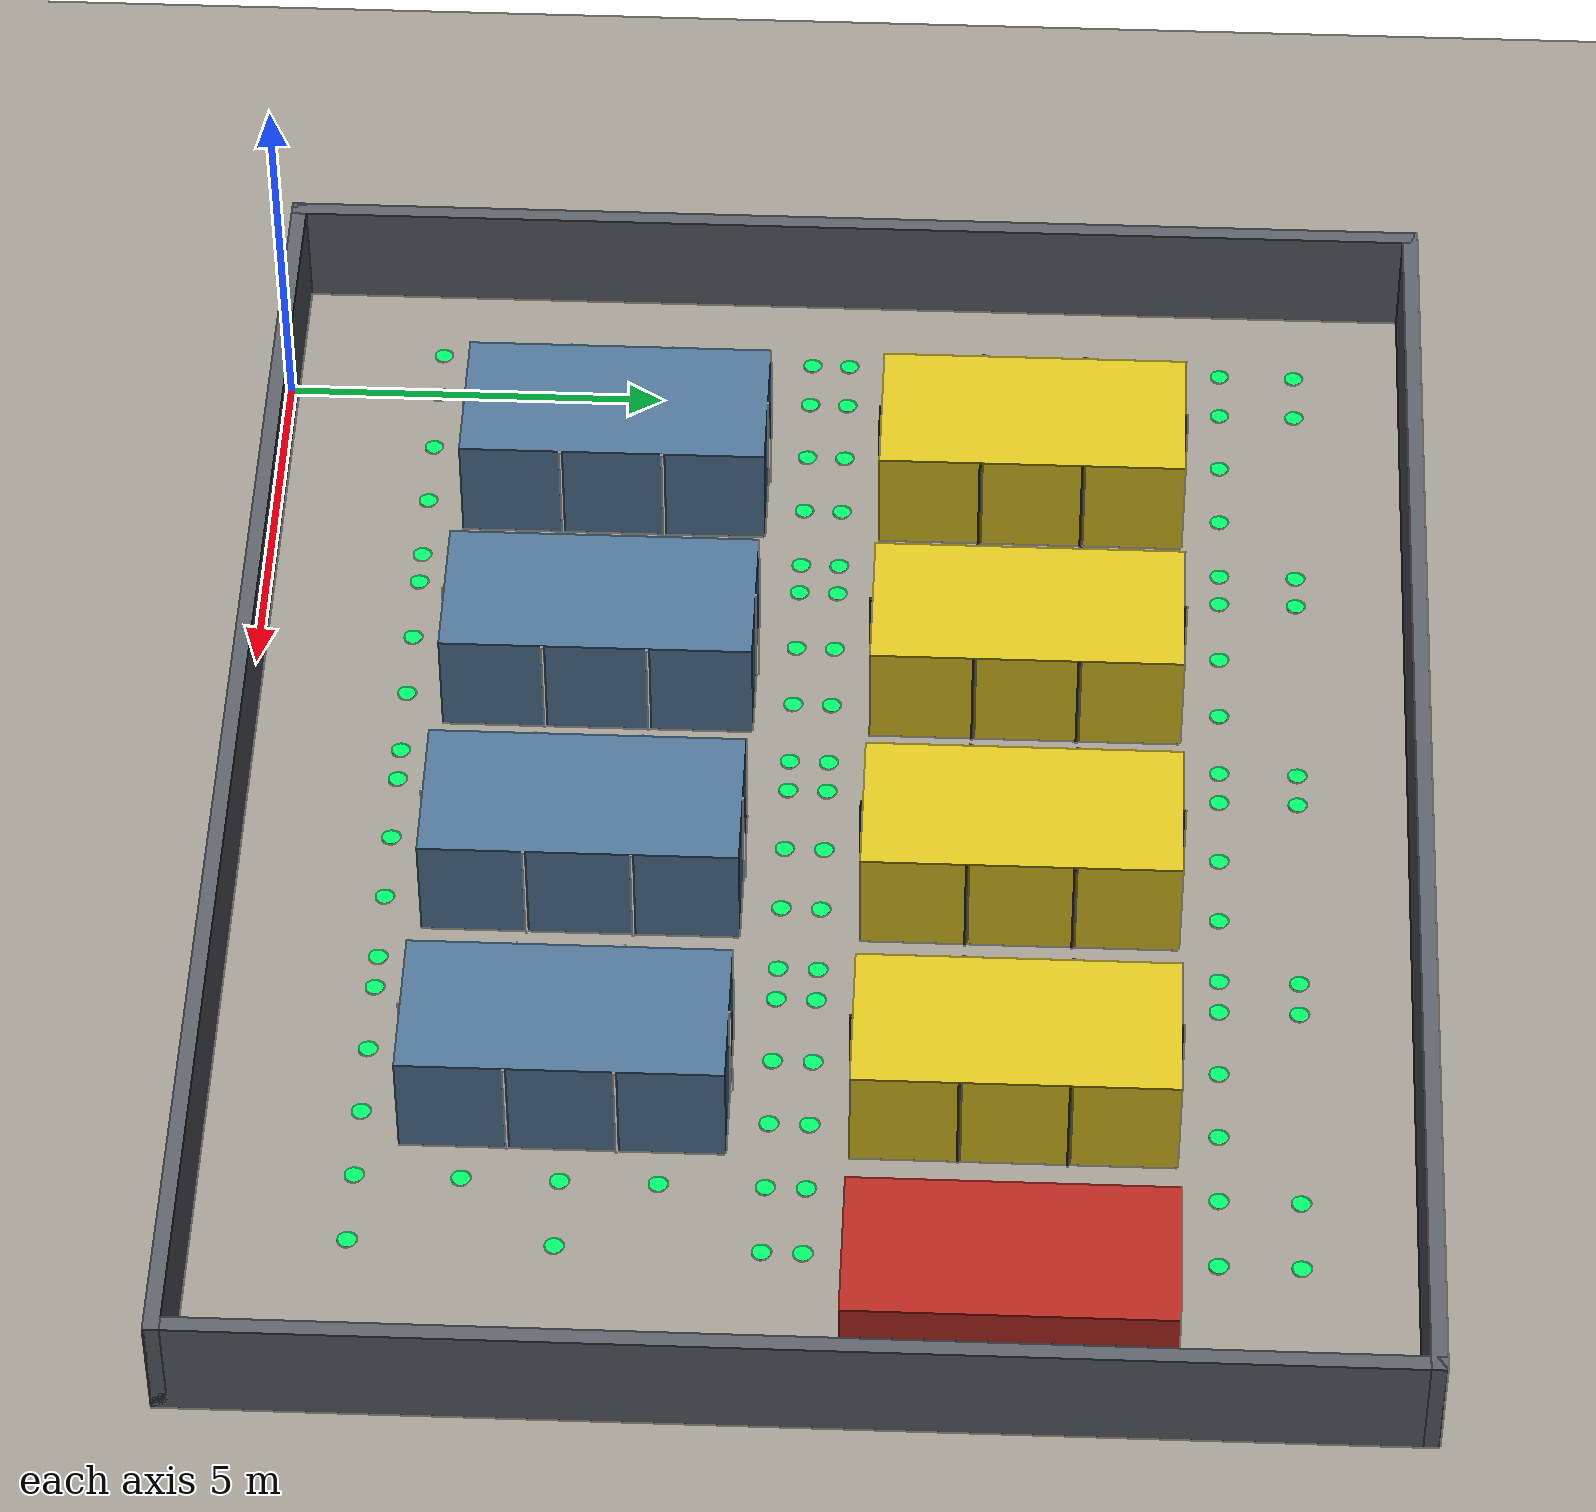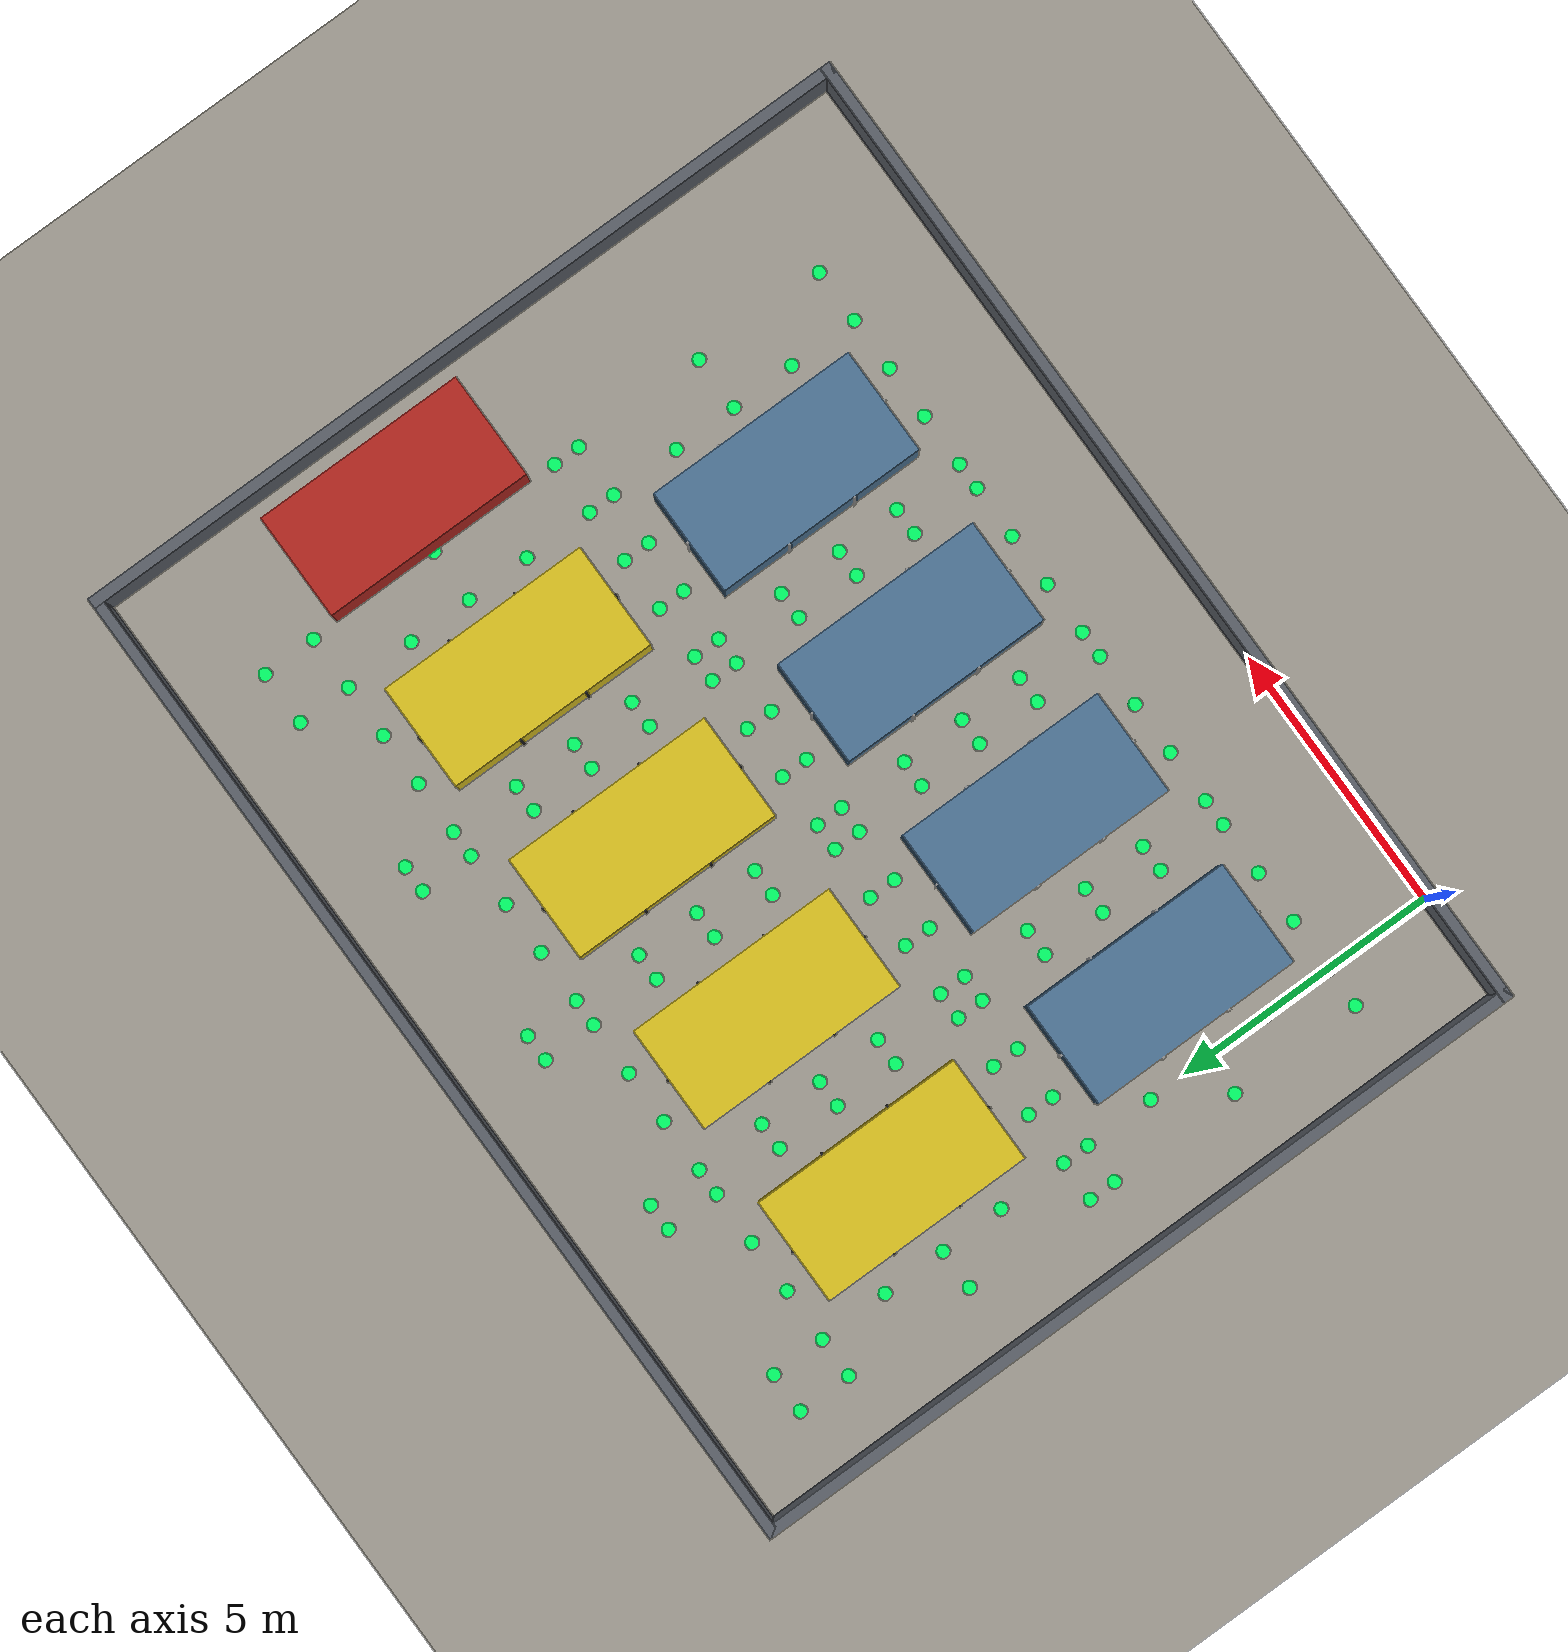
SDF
<?xml version="1.0" ?>
<sdf version="1.9">
  <world name="sih_warehouse">

    <!-- ===================== Physics & System Plugins ===================== -->
    <physics name="1ms" type="ignored">
      <max_step_size>0.001</max_step_size>
      <real_time_factor>1.0</real_time_factor>
    </physics>
    <plugin filename="gz-sim-physics-system" name="gz::sim::systems::Physics"/>
    <plugin filename="gz-sim-user-commands-system" name="gz::sim::systems::UserCommands"/>
    <plugin filename="gz-sim-scene-broadcaster-system" name="gz::sim::systems::SceneBroadcaster"/>
    <plugin filename="gz-sim-sensors-system" name="gz::sim::systems::Sensors">
      <render_engine>ogre2</render_engine>
    </plugin>
    <plugin filename="gz-sim-contact-system" name="gz::sim::systems::Contact"/>

    <!-- ===================== Scene & Ambient ===================== -->
    <scene>
      <ambient>0.4 0.4 0.45 1.0</ambient>
      <background>0.15 0.17 0.20 1.0</background>
      <shadows>true</shadows>
    </scene>

    <!-- Primary Overhead Light (Industrial High-Bay) -->
    <light type="directional" name="high_bay_main">
      <cast_shadows>true</cast_shadows>
      <pose>7.5 7.5 12 0 0 0</pose>
      <diffuse>0.92 0.90 0.85 1</diffuse>
      <specular>0.35 0.34 0.32 1</specular>
      <attenuation>
        <range>1000</range>
        <constant>0.9</constant>
        <linear>0.01</linear>
        <quadratic>0.001</quadratic>
      </attenuation>
      <direction>-0.3 0.1 -0.9</direction>
    </light>

    <!-- Secondary Fill Light (softer, bluish cool tone) -->
    <light type="directional" name="fill_light">
      <cast_shadows>false</cast_shadows>
      <pose>7.5 7.5 10 0 0 0</pose>
      <diffuse>0.3 0.35 0.45 1</diffuse>
      <specular>0.05 0.05 0.08 1</specular>
      <attenuation>
        <range>500</range>
        <constant>0.95</constant>
        <linear>0.005</linear>
        <quadratic>0.0005</quadratic>
      </attenuation>
      <direction>0.4 -0.2 -0.85</direction>
    </light>

    <!-- ===================== Ground Plane — Polished Concrete ===================== -->
    <model name="ground_plane">
      <static>true</static>
      <link name="link">
        <collision name="collision">
          <geometry><plane><normal>0 0 1</normal><size>100 100</size></plane></geometry>
        </collision>
        <visual name="visual">
          <geometry><plane><normal>0 0 1</normal><size>100 100</size></plane></geometry>
          <material>
            <ambient>0.55 0.53 0.50 1</ambient>
            <diffuse>0.62 0.60 0.56 1</diffuse>
            <specular>0.15 0.15 0.14 1</specular>
          </material>
        </visual>
      </link>
    </model>

    <!-- ===================== Outer Walls (Expanded Corridors X: -2.0m to 17.0m) ===================== -->
    <model name="wall_south">
      <static>true</static>
      <pose>7.5 0.0 0.75 0 0 0</pose>
      <link name="link">
        <collision name="col"><geometry><box><size>19.2 0.2 1.5</size></box></geometry></collision>
        <visual name="vis">
          <geometry><box><size>19.2 0.2 1.5</size></box></geometry>
          <material>
            <ambient>0.28 0.30 0.32 1</ambient>
            <diffuse>0.35 0.37 0.40 1</diffuse>
            <specular>0.08 0.08 0.08 1</specular>
          </material>
        </visual>
      </link>
    </model>
    <model name="wall_north">
      <static>true</static>
      <pose>7.5 15.0 0.75 0 0 0</pose>
      <link name="link">
        <collision name="col"><geometry><box><size>19.2 0.2 1.5</size></box></geometry></collision>
        <visual name="vis">
          <geometry><box><size>19.2 0.2 1.5</size></box></geometry>
          <material>
            <ambient>0.28 0.30 0.32 1</ambient>
            <diffuse>0.35 0.37 0.40 1</diffuse>
            <specular>0.08 0.08 0.08 1</specular>
          </material>
        </visual>
      </link>
    </model>
    <model name="wall_west">
      <static>true</static>
      <pose>-2.0 7.5 0.75 0 0 0</pose>
      <link name="link">
        <collision name="col"><geometry><box><size>0.2 15.2 1.5</size></box></geometry></collision>
        <visual name="vis">
          <geometry><box><size>0.2 15.2 1.5</size></box></geometry>
          <material>
            <ambient>0.28 0.30 0.32 1</ambient>
            <diffuse>0.35 0.37 0.40 1</diffuse>
            <specular>0.08 0.08 0.08 1</specular>
          </material>
        </visual>
      </link>
    </model>
    <model name="wall_east">
      <static>true</static>
      <pose>17.0 7.5 0.75 0 0 0</pose>
      <link name="link">
        <collision name="col"><geometry><box><size>0.2 15.2 1.5</size></box></geometry></collision>
        <visual name="vis">
          <geometry><box><size>0.2 15.2 1.5</size></box></geometry>
          <material>
            <ambient>0.28 0.30 0.32 1</ambient>
            <diffuse>0.35 0.37 0.40 1</diffuse>
            <specular>0.08 0.08 0.08 1</specular>
          </material>
        </visual>
      </link>
    </model>

    <!-- ===================== Row A Racks — Safety Yellow ===================== -->
    <model name="rack_1A">
      <static>true</static>
      <pose>1.5 10.0 0.75 0 0 0</pose>
      <link name="link">
        <collision name="col"><geometry><box><size>2 4 1.5</size></box></geometry></collision>
        <visual name="vis">
          <geometry><box><size>2 4 1.5</size></box></geometry>
          <material>
            <ambient>0.72 0.62 0.10 1</ambient>
            <diffuse>0.85 0.75 0.12 1</diffuse>
            <specular>0.20 0.18 0.05 1</specular>
          </material>
        </visual>
      </link>
    </model>
    <model name="rack_2A">
      <static>true</static>
      <pose>5.0 10.0 0.75 0 0 0</pose>
      <link name="link">
        <collision name="col"><geometry><box><size>2 4 1.5</size></box></geometry></collision>
        <visual name="vis">
          <geometry><box><size>2 4 1.5</size></box></geometry>
          <material>
            <ambient>0.72 0.62 0.10 1</ambient>
            <diffuse>0.85 0.75 0.12 1</diffuse>
            <specular>0.20 0.18 0.05 1</specular>
          </material>
        </visual>
      </link>
    </model>
    <model name="rack_3A">
      <static>true</static>
      <pose>8.5 10.0 0.75 0 0 0</pose>
      <link name="link">
        <collision name="col"><geometry><box><size>2 4 1.5</size></box></geometry></collision>
        <visual name="vis">
          <geometry><box><size>2 4 1.5</size></box></geometry>
          <material>
            <ambient>0.72 0.62 0.10 1</ambient>
            <diffuse>0.85 0.75 0.12 1</diffuse>
            <specular>0.20 0.18 0.05 1</specular>
          </material>
        </visual>
      </link>
    </model>
    <model name="rack_4A">
      <static>true</static>
      <pose>12.0 10.0 0.75 0 0 0</pose>
      <link name="link">
        <collision name="col"><geometry><box><size>2 4 1.5</size></box></geometry></collision>
        <visual name="vis">
          <geometry><box><size>2 4 1.5</size></box></geometry>
          <material>
            <ambient>0.72 0.62 0.10 1</ambient>
            <diffuse>0.85 0.75 0.12 1</diffuse>
            <specular>0.20 0.18 0.05 1</specular>
          </material>
        </visual>
      </link>
    </model>

    <!-- ===================== Row B Racks — Industrial Steel Blue ===================== -->
    <model name="rack_1B">
      <static>true</static>
      <pose>1.5 4.5 0.75 0 0 0</pose>
      <link name="link">
        <collision name="col"><geometry><box><size>2 4 1.5</size></box></geometry></collision>
        <visual name="vis">
          <geometry><box><size>2 4 1.5</size></box></geometry>
          <material>
            <ambient>0.22 0.35 0.48 1</ambient>
            <diffuse>0.30 0.45 0.58 1</diffuse>
            <specular>0.12 0.14 0.18 1</specular>
          </material>
        </visual>
      </link>
    </model>
    <model name="rack_2B">
      <static>true</static>
      <pose>5.0 4.5 0.75 0 0 0</pose>
      <link name="link">
        <collision name="col"><geometry><box><size>2 4 1.5</size></box></geometry></collision>
        <visual name="vis">
          <geometry><box><size>2 4 1.5</size></box></geometry>
          <material>
            <ambient>0.22 0.35 0.48 1</ambient>
            <diffuse>0.30 0.45 0.58 1</diffuse>
            <specular>0.12 0.14 0.18 1</specular>
          </material>
        </visual>
      </link>
    </model>
    <model name="rack_3B">
      <static>true</static>
      <pose>8.5 4.5 0.75 0 0 0</pose>
      <link name="link">
        <collision name="col"><geometry><box><size>2 4 1.5</size></box></geometry></collision>
        <visual name="vis">
          <geometry><box><size>2 4 1.5</size></box></geometry>
          <material>
            <ambient>0.22 0.35 0.48 1</ambient>
            <diffuse>0.30 0.45 0.58 1</diffuse>
            <specular>0.12 0.14 0.18 1</specular>
          </material>
        </visual>
      </link>
    </model>
    <model name="rack_4B">
      <static>true</static>
      <pose>12.0 4.5 0.75 0 0 0</pose>
      <link name="link">
        <collision name="col"><geometry><box><size>2 4 1.5</size></box></geometry></collision>
        <visual name="vis">
          <geometry><box><size>2 4 1.5</size></box></geometry>
          <material>
            <ambient>0.22 0.35 0.48 1</ambient>
            <diffuse>0.30 0.45 0.58 1</diffuse>
            <specular>0.12 0.14 0.18 1</specular>
          </material>
        </visual>
      </link>
    </model>

    <!-- ===================== Dead-End Trap Zone — Hazard Red ===================== -->
    <model name="trap_zone">
      <static>true</static>
      <pose>15.5 10.0 0.75 0 0 0</pose>
      <link name="link">
        <collision name="col"><geometry><box><size>2 4 1.5</size></box></geometry></collision>
        <visual name="vis">
          <geometry><box><size>2 4 1.5</size></box></geometry>
          <material>
            <ambient>0.55 0.12 0.10 1</ambient>
            <diffuse>0.70 0.15 0.12 1</diffuse>
            <specular>0.18 0.06 0.05 1</specular>
          </material>
        </visual>
      </link>
    </model>

    <!-- ===================== Visual Topological Graph Floor Markers (Green Dots - NO COLLISION) ===================== -->
    <model name="vis_node_0">
      <static>true</static>
      <pose>-0.75 2.0 0.005 0 0 0</pose>
      <link name="link">
        <visual name="vis">
          <geometry><cylinder><radius>0.12</radius><length>0.005</length></cylinder></geometry>
          <material>
            <ambient>0.0 0.8 0.3 1</ambient>
            <diffuse>0.0 1.0 0.4 1</diffuse>
            <emissive>0.0 0.4 0.15 1</emissive>
          </material>
        </visual>
      </link>
    </model>
    <model name="vis_node_1">
      <static>true</static>
      <pose>-0.75 4.5 0.005 0 0 0</pose>
      <link name="link">
        <visual name="vis">
          <geometry><cylinder><radius>0.12</radius><length>0.005</length></cylinder></geometry>
          <material>
            <ambient>0.0 0.8 0.3 1</ambient>
            <diffuse>0.0 1.0 0.4 1</diffuse>
            <emissive>0.0 0.4 0.15 1</emissive>
          </material>
        </visual>
      </link>
    </model>
    <model name="vis_node_2">
      <static>true</static>
      <pose>-0.75 7.0 0.005 0 0 0</pose>
      <link name="link">
        <visual name="vis">
          <geometry><cylinder><radius>0.12</radius><length>0.005</length></cylinder></geometry>
          <material>
            <ambient>0.0 0.8 0.3 1</ambient>
            <diffuse>0.0 1.0 0.4 1</diffuse>
            <emissive>0.0 0.4 0.15 1</emissive>
          </material>
        </visual>
      </link>
    </model>
    <model name="vis_node_3">
      <static>true</static>
      <pose>-0.75 7.5 0.005 0 0 0</pose>
      <link name="link">
        <visual name="vis">
          <geometry><cylinder><radius>0.12</radius><length>0.005</length></cylinder></geometry>
          <material>
            <ambient>0.0 0.8 0.3 1</ambient>
            <diffuse>0.0 1.0 0.4 1</diffuse>
            <emissive>0.0 0.4 0.15 1</emissive>
          </material>
        </visual>
      </link>
    </model>
    <model name="vis_node_4">
      <static>true</static>
      <pose>-0.75 10.0 0.005 0 0 0</pose>
      <link name="link">
        <visual name="vis">
          <geometry><cylinder><radius>0.12</radius><length>0.005</length></cylinder></geometry>
          <material>
            <ambient>0.0 0.8 0.3 1</ambient>
            <diffuse>0.0 1.0 0.4 1</diffuse>
            <emissive>0.0 0.4 0.15 1</emissive>
          </material>
        </visual>
      </link>
    </model>
    <model name="vis_node_5">
      <static>true</static>
      <pose>-0.75 12.5 0.005 0 0 0</pose>
      <link name="link">
        <visual name="vis">
          <geometry><cylinder><radius>0.12</radius><length>0.005</length></cylinder></geometry>
          <material>
            <ambient>0.0 0.8 0.3 1</ambient>
            <diffuse>0.0 1.0 0.4 1</diffuse>
            <emissive>0.0 0.4 0.15 1</emissive>
          </material>
        </visual>
      </link>
    </model>
    <model name="vis_node_6">
      <static>true</static>
      <pose>-0.75 13.5 0.005 0 0 0</pose>
      <link name="link">
        <visual name="vis">
          <geometry><cylinder><radius>0.12</radius><length>0.005</length></cylinder></geometry>
          <material>
            <ambient>0.0 0.8 0.3 1</ambient>
            <diffuse>0.0 1.0 0.4 1</diffuse>
            <emissive>0.0 0.4 0.15 1</emissive>
          </material>
        </visual>
      </link>
    </model>
    <model name="vis_node_7">
      <static>true</static>
      <pose>0.0 2.0 0.005 0 0 0</pose>
      <link name="link">
        <visual name="vis">
          <geometry><cylinder><radius>0.12</radius><length>0.005</length></cylinder></geometry>
          <material>
            <ambient>0.0 0.8 0.3 1</ambient>
            <diffuse>0.0 1.0 0.4 1</diffuse>
            <emissive>0.0 0.4 0.15 1</emissive>
          </material>
        </visual>
      </link>
    </model>
    <model name="vis_node_8">
      <static>true</static>
      <pose>0.0 4.5 0.005 0 0 0</pose>
      <link name="link">
        <visual name="vis">
          <geometry><cylinder><radius>0.12</radius><length>0.005</length></cylinder></geometry>
          <material>
            <ambient>0.0 0.8 0.3 1</ambient>
            <diffuse>0.0 1.0 0.4 1</diffuse>
            <emissive>0.0 0.4 0.15 1</emissive>
          </material>
        </visual>
      </link>
    </model>
    <model name="vis_node_9">
      <static>true</static>
      <pose>0.0 7.0 0.005 0 0 0</pose>
      <link name="link">
        <visual name="vis">
          <geometry><cylinder><radius>0.12</radius><length>0.005</length></cylinder></geometry>
          <material>
            <ambient>0.0 0.8 0.3 1</ambient>
            <diffuse>0.0 1.0 0.4 1</diffuse>
            <emissive>0.0 0.4 0.15 1</emissive>
          </material>
        </visual>
      </link>
    </model>
    <model name="vis_node_10">
      <static>true</static>
      <pose>0.0 7.5 0.005 0 0 0</pose>
      <link name="link">
        <visual name="vis">
          <geometry><cylinder><radius>0.12</radius><length>0.005</length></cylinder></geometry>
          <material>
            <ambient>0.0 0.8 0.3 1</ambient>
            <diffuse>0.0 1.0 0.4 1</diffuse>
            <emissive>0.0 0.4 0.15 1</emissive>
          </material>
        </visual>
      </link>
    </model>
    <model name="vis_node_11">
      <static>true</static>
      <pose>0.0 10.0 0.005 0 0 0</pose>
      <link name="link">
        <visual name="vis">
          <geometry><cylinder><radius>0.12</radius><length>0.005</length></cylinder></geometry>
          <material>
            <ambient>0.0 0.8 0.3 1</ambient>
            <diffuse>0.0 1.0 0.4 1</diffuse>
            <emissive>0.0 0.4 0.15 1</emissive>
          </material>
        </visual>
      </link>
    </model>
    <model name="vis_node_12">
      <static>true</static>
      <pose>0.0 12.5 0.005 0 0 0</pose>
      <link name="link">
        <visual name="vis">
          <geometry><cylinder><radius>0.12</radius><length>0.005</length></cylinder></geometry>
          <material>
            <ambient>0.0 0.8 0.3 1</ambient>
            <diffuse>0.0 1.0 0.4 1</diffuse>
            <emissive>0.0 0.4 0.15 1</emissive>
          </material>
        </visual>
      </link>
    </model>
    <model name="vis_node_13">
      <static>true</static>
      <pose>0.0 13.5 0.005 0 0 0</pose>
      <link name="link">
        <visual name="vis">
          <geometry><cylinder><radius>0.12</radius><length>0.005</length></cylinder></geometry>
          <material>
            <ambient>0.0 0.8 0.3 1</ambient>
            <diffuse>0.0 1.0 0.4 1</diffuse>
            <emissive>0.0 0.4 0.15 1</emissive>
          </material>
        </visual>
      </link>
    </model>
    <model name="vis_node_14">
      <static>true</static>
      <pose>3.0 2.0 0.005 0 0 0</pose>
      <link name="link">
        <visual name="vis">
          <geometry><cylinder><radius>0.12</radius><length>0.005</length></cylinder></geometry>
          <material>
            <ambient>0.0 0.8 0.3 1</ambient>
            <diffuse>0.0 1.0 0.4 1</diffuse>
            <emissive>0.0 0.4 0.15 1</emissive>
          </material>
        </visual>
      </link>
    </model>
    <model name="vis_node_15">
      <static>true</static>
      <pose>3.0 4.5 0.005 0 0 0</pose>
      <link name="link">
        <visual name="vis">
          <geometry><cylinder><radius>0.12</radius><length>0.005</length></cylinder></geometry>
          <material>
            <ambient>0.0 0.8 0.3 1</ambient>
            <diffuse>0.0 1.0 0.4 1</diffuse>
            <emissive>0.0 0.4 0.15 1</emissive>
          </material>
        </visual>
      </link>
    </model>
    <model name="vis_node_16">
      <static>true</static>
      <pose>3.0 7.0 0.005 0 0 0</pose>
      <link name="link">
        <visual name="vis">
          <geometry><cylinder><radius>0.12</radius><length>0.005</length></cylinder></geometry>
          <material>
            <ambient>0.0 0.8 0.3 1</ambient>
            <diffuse>0.0 1.0 0.4 1</diffuse>
            <emissive>0.0 0.4 0.15 1</emissive>
          </material>
        </visual>
      </link>
    </model>
    <model name="vis_node_17">
      <static>true</static>
      <pose>3.0 7.5 0.005 0 0 0</pose>
      <link name="link">
        <visual name="vis">
          <geometry><cylinder><radius>0.12</radius><length>0.005</length></cylinder></geometry>
          <material>
            <ambient>0.0 0.8 0.3 1</ambient>
            <diffuse>0.0 1.0 0.4 1</diffuse>
            <emissive>0.0 0.4 0.15 1</emissive>
          </material>
        </visual>
      </link>
    </model>
    <model name="vis_node_18">
      <static>true</static>
      <pose>3.0 10.0 0.005 0 0 0</pose>
      <link name="link">
        <visual name="vis">
          <geometry><cylinder><radius>0.12</radius><length>0.005</length></cylinder></geometry>
          <material>
            <ambient>0.0 0.8 0.3 1</ambient>
            <diffuse>0.0 1.0 0.4 1</diffuse>
            <emissive>0.0 0.4 0.15 1</emissive>
          </material>
        </visual>
      </link>
    </model>
    <model name="vis_node_19">
      <static>true</static>
      <pose>3.0 12.5 0.005 0 0 0</pose>
      <link name="link">
        <visual name="vis">
          <geometry><cylinder><radius>0.12</radius><length>0.005</length></cylinder></geometry>
          <material>
            <ambient>0.0 0.8 0.3 1</ambient>
            <diffuse>0.0 1.0 0.4 1</diffuse>
            <emissive>0.0 0.4 0.15 1</emissive>
          </material>
        </visual>
      </link>
    </model>
    <model name="vis_node_20">
      <static>true</static>
      <pose>3.0 13.5 0.005 0 0 0</pose>
      <link name="link">
        <visual name="vis">
          <geometry><cylinder><radius>0.12</radius><length>0.005</length></cylinder></geometry>
          <material>
            <ambient>0.0 0.8 0.3 1</ambient>
            <diffuse>0.0 1.0 0.4 1</diffuse>
            <emissive>0.0 0.4 0.15 1</emissive>
          </material>
        </visual>
      </link>
    </model>
    <model name="vis_node_21">
      <static>true</static>
      <pose>3.5 2.0 0.005 0 0 0</pose>
      <link name="link">
        <visual name="vis">
          <geometry><cylinder><radius>0.12</radius><length>0.005</length></cylinder></geometry>
          <material>
            <ambient>0.0 0.8 0.3 1</ambient>
            <diffuse>0.0 1.0 0.4 1</diffuse>
            <emissive>0.0 0.4 0.15 1</emissive>
          </material>
        </visual>
      </link>
    </model>
    <model name="vis_node_22">
      <static>true</static>
      <pose>3.5 4.5 0.005 0 0 0</pose>
      <link name="link">
        <visual name="vis">
          <geometry><cylinder><radius>0.12</radius><length>0.005</length></cylinder></geometry>
          <material>
            <ambient>0.0 0.8 0.3 1</ambient>
            <diffuse>0.0 1.0 0.4 1</diffuse>
            <emissive>0.0 0.4 0.15 1</emissive>
          </material>
        </visual>
      </link>
    </model>
    <model name="vis_node_23">
      <static>true</static>
      <pose>3.5 7.0 0.005 0 0 0</pose>
      <link name="link">
        <visual name="vis">
          <geometry><cylinder><radius>0.12</radius><length>0.005</length></cylinder></geometry>
          <material>
            <ambient>0.0 0.8 0.3 1</ambient>
            <diffuse>0.0 1.0 0.4 1</diffuse>
            <emissive>0.0 0.4 0.15 1</emissive>
          </material>
        </visual>
      </link>
    </model>
    <model name="vis_node_24">
      <static>true</static>
      <pose>3.5 7.5 0.005 0 0 0</pose>
      <link name="link">
        <visual name="vis">
          <geometry><cylinder><radius>0.12</radius><length>0.005</length></cylinder></geometry>
          <material>
            <ambient>0.0 0.8 0.3 1</ambient>
            <diffuse>0.0 1.0 0.4 1</diffuse>
            <emissive>0.0 0.4 0.15 1</emissive>
          </material>
        </visual>
      </link>
    </model>
    <model name="vis_node_25">
      <static>true</static>
      <pose>3.5 10.0 0.005 0 0 0</pose>
      <link name="link">
        <visual name="vis">
          <geometry><cylinder><radius>0.12</radius><length>0.005</length></cylinder></geometry>
          <material>
            <ambient>0.0 0.8 0.3 1</ambient>
            <diffuse>0.0 1.0 0.4 1</diffuse>
            <emissive>0.0 0.4 0.15 1</emissive>
          </material>
        </visual>
      </link>
    </model>
    <model name="vis_node_26">
      <static>true</static>
      <pose>3.5 12.5 0.005 0 0 0</pose>
      <link name="link">
        <visual name="vis">
          <geometry><cylinder><radius>0.12</radius><length>0.005</length></cylinder></geometry>
          <material>
            <ambient>0.0 0.8 0.3 1</ambient>
            <diffuse>0.0 1.0 0.4 1</diffuse>
            <emissive>0.0 0.4 0.15 1</emissive>
          </material>
        </visual>
      </link>
    </model>
    <model name="vis_node_27">
      <static>true</static>
      <pose>3.5 13.5 0.005 0 0 0</pose>
      <link name="link">
        <visual name="vis">
          <geometry><cylinder><radius>0.12</radius><length>0.005</length></cylinder></geometry>
          <material>
            <ambient>0.0 0.8 0.3 1</ambient>
            <diffuse>0.0 1.0 0.4 1</diffuse>
            <emissive>0.0 0.4 0.15 1</emissive>
          </material>
        </visual>
      </link>
    </model>
    <model name="vis_node_28">
      <static>true</static>
      <pose>6.5 2.0 0.005 0 0 0</pose>
      <link name="link">
        <visual name="vis">
          <geometry><cylinder><radius>0.12</radius><length>0.005</length></cylinder></geometry>
          <material>
            <ambient>0.0 0.8 0.3 1</ambient>
            <diffuse>0.0 1.0 0.4 1</diffuse>
            <emissive>0.0 0.4 0.15 1</emissive>
          </material>
        </visual>
      </link>
    </model>
    <model name="vis_node_29">
      <static>true</static>
      <pose>6.5 4.5 0.005 0 0 0</pose>
      <link name="link">
        <visual name="vis">
          <geometry><cylinder><radius>0.12</radius><length>0.005</length></cylinder></geometry>
          <material>
            <ambient>0.0 0.8 0.3 1</ambient>
            <diffuse>0.0 1.0 0.4 1</diffuse>
            <emissive>0.0 0.4 0.15 1</emissive>
          </material>
        </visual>
      </link>
    </model>
    <model name="vis_node_30">
      <static>true</static>
      <pose>6.5 7.0 0.005 0 0 0</pose>
      <link name="link">
        <visual name="vis">
          <geometry><cylinder><radius>0.12</radius><length>0.005</length></cylinder></geometry>
          <material>
            <ambient>0.0 0.8 0.3 1</ambient>
            <diffuse>0.0 1.0 0.4 1</diffuse>
            <emissive>0.0 0.4 0.15 1</emissive>
          </material>
        </visual>
      </link>
    </model>
    <model name="vis_node_31">
      <static>true</static>
      <pose>6.5 7.5 0.005 0 0 0</pose>
      <link name="link">
        <visual name="vis">
          <geometry><cylinder><radius>0.12</radius><length>0.005</length></cylinder></geometry>
          <material>
            <ambient>0.0 0.8 0.3 1</ambient>
            <diffuse>0.0 1.0 0.4 1</diffuse>
            <emissive>0.0 0.4 0.15 1</emissive>
          </material>
        </visual>
      </link>
    </model>
    <model name="vis_node_32">
      <static>true</static>
      <pose>6.5 10.0 0.005 0 0 0</pose>
      <link name="link">
        <visual name="vis">
          <geometry><cylinder><radius>0.12</radius><length>0.005</length></cylinder></geometry>
          <material>
            <ambient>0.0 0.8 0.3 1</ambient>
            <diffuse>0.0 1.0 0.4 1</diffuse>
            <emissive>0.0 0.4 0.15 1</emissive>
          </material>
        </visual>
      </link>
    </model>
    <model name="vis_node_33">
      <static>true</static>
      <pose>6.5 12.5 0.005 0 0 0</pose>
      <link name="link">
        <visual name="vis">
          <geometry><cylinder><radius>0.12</radius><length>0.005</length></cylinder></geometry>
          <material>
            <ambient>0.0 0.8 0.3 1</ambient>
            <diffuse>0.0 1.0 0.4 1</diffuse>
            <emissive>0.0 0.4 0.15 1</emissive>
          </material>
        </visual>
      </link>
    </model>
    <model name="vis_node_34">
      <static>true</static>
      <pose>6.5 13.5 0.005 0 0 0</pose>
      <link name="link">
        <visual name="vis">
          <geometry><cylinder><radius>0.12</radius><length>0.005</length></cylinder></geometry>
          <material>
            <ambient>0.0 0.8 0.3 1</ambient>
            <diffuse>0.0 1.0 0.4 1</diffuse>
            <emissive>0.0 0.4 0.15 1</emissive>
          </material>
        </visual>
      </link>
    </model>
    <model name="vis_node_35">
      <static>true</static>
      <pose>7.0 2.0 0.005 0 0 0</pose>
      <link name="link">
        <visual name="vis">
          <geometry><cylinder><radius>0.12</radius><length>0.005</length></cylinder></geometry>
          <material>
            <ambient>0.0 0.8 0.3 1</ambient>
            <diffuse>0.0 1.0 0.4 1</diffuse>
            <emissive>0.0 0.4 0.15 1</emissive>
          </material>
        </visual>
      </link>
    </model>
    <model name="vis_node_36">
      <static>true</static>
      <pose>7.0 4.5 0.005 0 0 0</pose>
      <link name="link">
        <visual name="vis">
          <geometry><cylinder><radius>0.12</radius><length>0.005</length></cylinder></geometry>
          <material>
            <ambient>0.0 0.8 0.3 1</ambient>
            <diffuse>0.0 1.0 0.4 1</diffuse>
            <emissive>0.0 0.4 0.15 1</emissive>
          </material>
        </visual>
      </link>
    </model>
    <model name="vis_node_37">
      <static>true</static>
      <pose>7.0 7.0 0.005 0 0 0</pose>
      <link name="link">
        <visual name="vis">
          <geometry><cylinder><radius>0.12</radius><length>0.005</length></cylinder></geometry>
          <material>
            <ambient>0.0 0.8 0.3 1</ambient>
            <diffuse>0.0 1.0 0.4 1</diffuse>
            <emissive>0.0 0.4 0.15 1</emissive>
          </material>
        </visual>
      </link>
    </model>
    <model name="vis_node_38">
      <static>true</static>
      <pose>7.0 7.5 0.005 0 0 0</pose>
      <link name="link">
        <visual name="vis">
          <geometry><cylinder><radius>0.12</radius><length>0.005</length></cylinder></geometry>
          <material>
            <ambient>0.0 0.8 0.3 1</ambient>
            <diffuse>0.0 1.0 0.4 1</diffuse>
            <emissive>0.0 0.4 0.15 1</emissive>
          </material>
        </visual>
      </link>
    </model>
    <model name="vis_node_39">
      <static>true</static>
      <pose>7.0 10.0 0.005 0 0 0</pose>
      <link name="link">
        <visual name="vis">
          <geometry><cylinder><radius>0.12</radius><length>0.005</length></cylinder></geometry>
          <material>
            <ambient>0.0 0.8 0.3 1</ambient>
            <diffuse>0.0 1.0 0.4 1</diffuse>
            <emissive>0.0 0.4 0.15 1</emissive>
          </material>
        </visual>
      </link>
    </model>
    <model name="vis_node_40">
      <static>true</static>
      <pose>7.0 12.5 0.005 0 0 0</pose>
      <link name="link">
        <visual name="vis">
          <geometry><cylinder><radius>0.12</radius><length>0.005</length></cylinder></geometry>
          <material>
            <ambient>0.0 0.8 0.3 1</ambient>
            <diffuse>0.0 1.0 0.4 1</diffuse>
            <emissive>0.0 0.4 0.15 1</emissive>
          </material>
        </visual>
      </link>
    </model>
    <model name="vis_node_41">
      <static>true</static>
      <pose>7.0 13.5 0.005 0 0 0</pose>
      <link name="link">
        <visual name="vis">
          <geometry><cylinder><radius>0.12</radius><length>0.005</length></cylinder></geometry>
          <material>
            <ambient>0.0 0.8 0.3 1</ambient>
            <diffuse>0.0 1.0 0.4 1</diffuse>
            <emissive>0.0 0.4 0.15 1</emissive>
          </material>
        </visual>
      </link>
    </model>
    <model name="vis_node_42">
      <static>true</static>
      <pose>10.0 2.0 0.005 0 0 0</pose>
      <link name="link">
        <visual name="vis">
          <geometry><cylinder><radius>0.12</radius><length>0.005</length></cylinder></geometry>
          <material>
            <ambient>0.0 0.8 0.3 1</ambient>
            <diffuse>0.0 1.0 0.4 1</diffuse>
            <emissive>0.0 0.4 0.15 1</emissive>
          </material>
        </visual>
      </link>
    </model>
    <model name="vis_node_43">
      <static>true</static>
      <pose>10.0 4.5 0.005 0 0 0</pose>
      <link name="link">
        <visual name="vis">
          <geometry><cylinder><radius>0.12</radius><length>0.005</length></cylinder></geometry>
          <material>
            <ambient>0.0 0.8 0.3 1</ambient>
            <diffuse>0.0 1.0 0.4 1</diffuse>
            <emissive>0.0 0.4 0.15 1</emissive>
          </material>
        </visual>
      </link>
    </model>
    <model name="vis_node_44">
      <static>true</static>
      <pose>10.0 7.0 0.005 0 0 0</pose>
      <link name="link">
        <visual name="vis">
          <geometry><cylinder><radius>0.12</radius><length>0.005</length></cylinder></geometry>
          <material>
            <ambient>0.0 0.8 0.3 1</ambient>
            <diffuse>0.0 1.0 0.4 1</diffuse>
            <emissive>0.0 0.4 0.15 1</emissive>
          </material>
        </visual>
      </link>
    </model>
    <model name="vis_node_45">
      <static>true</static>
      <pose>10.0 7.5 0.005 0 0 0</pose>
      <link name="link">
        <visual name="vis">
          <geometry><cylinder><radius>0.12</radius><length>0.005</length></cylinder></geometry>
          <material>
            <ambient>0.0 0.8 0.3 1</ambient>
            <diffuse>0.0 1.0 0.4 1</diffuse>
            <emissive>0.0 0.4 0.15 1</emissive>
          </material>
        </visual>
      </link>
    </model>
    <model name="vis_node_46">
      <static>true</static>
      <pose>10.0 10.0 0.005 0 0 0</pose>
      <link name="link">
        <visual name="vis">
          <geometry><cylinder><radius>0.12</radius><length>0.005</length></cylinder></geometry>
          <material>
            <ambient>0.0 0.8 0.3 1</ambient>
            <diffuse>0.0 1.0 0.4 1</diffuse>
            <emissive>0.0 0.4 0.15 1</emissive>
          </material>
        </visual>
      </link>
    </model>
    <model name="vis_node_47">
      <static>true</static>
      <pose>10.0 12.5 0.005 0 0 0</pose>
      <link name="link">
        <visual name="vis">
          <geometry><cylinder><radius>0.12</radius><length>0.005</length></cylinder></geometry>
          <material>
            <ambient>0.0 0.8 0.3 1</ambient>
            <diffuse>0.0 1.0 0.4 1</diffuse>
            <emissive>0.0 0.4 0.15 1</emissive>
          </material>
        </visual>
      </link>
    </model>
    <model name="vis_node_48">
      <static>true</static>
      <pose>10.0 13.5 0.005 0 0 0</pose>
      <link name="link">
        <visual name="vis">
          <geometry><cylinder><radius>0.12</radius><length>0.005</length></cylinder></geometry>
          <material>
            <ambient>0.0 0.8 0.3 1</ambient>
            <diffuse>0.0 1.0 0.4 1</diffuse>
            <emissive>0.0 0.4 0.15 1</emissive>
          </material>
        </visual>
      </link>
    </model>
    <model name="vis_node_49">
      <static>true</static>
      <pose>10.5 2.0 0.005 0 0 0</pose>
      <link name="link">
        <visual name="vis">
          <geometry><cylinder><radius>0.12</radius><length>0.005</length></cylinder></geometry>
          <material>
            <ambient>0.0 0.8 0.3 1</ambient>
            <diffuse>0.0 1.0 0.4 1</diffuse>
            <emissive>0.0 0.4 0.15 1</emissive>
          </material>
        </visual>
      </link>
    </model>
    <model name="vis_node_50">
      <static>true</static>
      <pose>10.5 4.5 0.005 0 0 0</pose>
      <link name="link">
        <visual name="vis">
          <geometry><cylinder><radius>0.12</radius><length>0.005</length></cylinder></geometry>
          <material>
            <ambient>0.0 0.8 0.3 1</ambient>
            <diffuse>0.0 1.0 0.4 1</diffuse>
            <emissive>0.0 0.4 0.15 1</emissive>
          </material>
        </visual>
      </link>
    </model>
    <model name="vis_node_51">
      <static>true</static>
      <pose>10.5 7.0 0.005 0 0 0</pose>
      <link name="link">
        <visual name="vis">
          <geometry><cylinder><radius>0.12</radius><length>0.005</length></cylinder></geometry>
          <material>
            <ambient>0.0 0.8 0.3 1</ambient>
            <diffuse>0.0 1.0 0.4 1</diffuse>
            <emissive>0.0 0.4 0.15 1</emissive>
          </material>
        </visual>
      </link>
    </model>
    <model name="vis_node_52">
      <static>true</static>
      <pose>10.5 7.5 0.005 0 0 0</pose>
      <link name="link">
        <visual name="vis">
          <geometry><cylinder><radius>0.12</radius><length>0.005</length></cylinder></geometry>
          <material>
            <ambient>0.0 0.8 0.3 1</ambient>
            <diffuse>0.0 1.0 0.4 1</diffuse>
            <emissive>0.0 0.4 0.15 1</emissive>
          </material>
        </visual>
      </link>
    </model>
    <model name="vis_node_53">
      <static>true</static>
      <pose>10.5 10.0 0.005 0 0 0</pose>
      <link name="link">
        <visual name="vis">
          <geometry><cylinder><radius>0.12</radius><length>0.005</length></cylinder></geometry>
          <material>
            <ambient>0.0 0.8 0.3 1</ambient>
            <diffuse>0.0 1.0 0.4 1</diffuse>
            <emissive>0.0 0.4 0.15 1</emissive>
          </material>
        </visual>
      </link>
    </model>
    <model name="vis_node_54">
      <static>true</static>
      <pose>10.5 12.5 0.005 0 0 0</pose>
      <link name="link">
        <visual name="vis">
          <geometry><cylinder><radius>0.12</radius><length>0.005</length></cylinder></geometry>
          <material>
            <ambient>0.0 0.8 0.3 1</ambient>
            <diffuse>0.0 1.0 0.4 1</diffuse>
            <emissive>0.0 0.4 0.15 1</emissive>
          </material>
        </visual>
      </link>
    </model>
    <model name="vis_node_55">
      <static>true</static>
      <pose>10.5 13.5 0.005 0 0 0</pose>
      <link name="link">
        <visual name="vis">
          <geometry><cylinder><radius>0.12</radius><length>0.005</length></cylinder></geometry>
          <material>
            <ambient>0.0 0.8 0.3 1</ambient>
            <diffuse>0.0 1.0 0.4 1</diffuse>
            <emissive>0.0 0.4 0.15 1</emissive>
          </material>
        </visual>
      </link>
    </model>
    <model name="vis_node_56">
      <static>true</static>
      <pose>13.5 2.0 0.005 0 0 0</pose>
      <link name="link">
        <visual name="vis">
          <geometry><cylinder><radius>0.12</radius><length>0.005</length></cylinder></geometry>
          <material>
            <ambient>0.0 0.8 0.3 1</ambient>
            <diffuse>0.0 1.0 0.4 1</diffuse>
            <emissive>0.0 0.4 0.15 1</emissive>
          </material>
        </visual>
      </link>
    </model>
    <model name="vis_node_57">
      <static>true</static>
      <pose>13.5 4.5 0.005 0 0 0</pose>
      <link name="link">
        <visual name="vis">
          <geometry><cylinder><radius>0.12</radius><length>0.005</length></cylinder></geometry>
          <material>
            <ambient>0.0 0.8 0.3 1</ambient>
            <diffuse>0.0 1.0 0.4 1</diffuse>
            <emissive>0.0 0.4 0.15 1</emissive>
          </material>
        </visual>
      </link>
    </model>
    <model name="vis_node_58">
      <static>true</static>
      <pose>13.5 7.0 0.005 0 0 0</pose>
      <link name="link">
        <visual name="vis">
          <geometry><cylinder><radius>0.12</radius><length>0.005</length></cylinder></geometry>
          <material>
            <ambient>0.0 0.8 0.3 1</ambient>
            <diffuse>0.0 1.0 0.4 1</diffuse>
            <emissive>0.0 0.4 0.15 1</emissive>
          </material>
        </visual>
      </link>
    </model>
    <model name="vis_node_59">
      <static>true</static>
      <pose>13.5 7.5 0.005 0 0 0</pose>
      <link name="link">
        <visual name="vis">
          <geometry><cylinder><radius>0.12</radius><length>0.005</length></cylinder></geometry>
          <material>
            <ambient>0.0 0.8 0.3 1</ambient>
            <diffuse>0.0 1.0 0.4 1</diffuse>
            <emissive>0.0 0.4 0.15 1</emissive>
          </material>
        </visual>
      </link>
    </model>
    <model name="vis_node_60">
      <static>true</static>
      <pose>13.5 10.0 0.005 0 0 0</pose>
      <link name="link">
        <visual name="vis">
          <geometry><cylinder><radius>0.12</radius><length>0.005</length></cylinder></geometry>
          <material>
            <ambient>0.0 0.8 0.3 1</ambient>
            <diffuse>0.0 1.0 0.4 1</diffuse>
            <emissive>0.0 0.4 0.15 1</emissive>
          </material>
        </visual>
      </link>
    </model>
    <model name="vis_node_61">
      <static>true</static>
      <pose>13.5 12.5 0.005 0 0 0</pose>
      <link name="link">
        <visual name="vis">
          <geometry><cylinder><radius>0.12</radius><length>0.005</length></cylinder></geometry>
          <material>
            <ambient>0.0 0.8 0.3 1</ambient>
            <diffuse>0.0 1.0 0.4 1</diffuse>
            <emissive>0.0 0.4 0.15 1</emissive>
          </material>
        </visual>
      </link>
    </model>
    <model name="vis_node_62">
      <static>true</static>
      <pose>13.5 13.5 0.005 0 0 0</pose>
      <link name="link">
        <visual name="vis">
          <geometry><cylinder><radius>0.12</radius><length>0.005</length></cylinder></geometry>
          <material>
            <ambient>0.0 0.8 0.3 1</ambient>
            <diffuse>0.0 1.0 0.4 1</diffuse>
            <emissive>0.0 0.4 0.15 1</emissive>
          </material>
        </visual>
      </link>
    </model>
    <model name="vis_node_63">
      <static>true</static>
      <pose>14.5 2.0 0.005 0 0 0</pose>
      <link name="link">
        <visual name="vis">
          <geometry><cylinder><radius>0.12</radius><length>0.005</length></cylinder></geometry>
          <material>
            <ambient>0.0 0.8 0.3 1</ambient>
            <diffuse>0.0 1.0 0.4 1</diffuse>
            <emissive>0.0 0.4 0.15 1</emissive>
          </material>
        </visual>
      </link>
    </model>
    <model name="vis_node_64">
      <static>true</static>
      <pose>14.5 4.5 0.005 0 0 0</pose>
      <link name="link">
        <visual name="vis">
          <geometry><cylinder><radius>0.12</radius><length>0.005</length></cylinder></geometry>
          <material>
            <ambient>0.0 0.8 0.3 1</ambient>
            <diffuse>0.0 1.0 0.4 1</diffuse>
            <emissive>0.0 0.4 0.15 1</emissive>
          </material>
        </visual>
      </link>
    </model>
    <model name="vis_node_65">
      <static>true</static>
      <pose>14.5 7.0 0.005 0 0 0</pose>
      <link name="link">
        <visual name="vis">
          <geometry><cylinder><radius>0.12</radius><length>0.005</length></cylinder></geometry>
          <material>
            <ambient>0.0 0.8 0.3 1</ambient>
            <diffuse>0.0 1.0 0.4 1</diffuse>
            <emissive>0.0 0.4 0.15 1</emissive>
          </material>
        </visual>
      </link>
    </model>
    <model name="vis_node_66">
      <static>true</static>
      <pose>14.5 7.5 0.005 0 0 0</pose>
      <link name="link">
        <visual name="vis">
          <geometry><cylinder><radius>0.12</radius><length>0.005</length></cylinder></geometry>
          <material>
            <ambient>0.0 0.8 0.3 1</ambient>
            <diffuse>0.0 1.0 0.4 1</diffuse>
            <emissive>0.0 0.4 0.15 1</emissive>
          </material>
        </visual>
      </link>
    </model>
    <model name="vis_node_67">
      <static>true</static>
      <pose>14.5 10.0 0.005 0 0 0</pose>
      <link name="link">
        <visual name="vis">
          <geometry><cylinder><radius>0.12</radius><length>0.005</length></cylinder></geometry>
          <material>
            <ambient>0.0 0.8 0.3 1</ambient>
            <diffuse>0.0 1.0 0.4 1</diffuse>
            <emissive>0.0 0.4 0.15 1</emissive>
          </material>
        </visual>
      </link>
    </model>
    <model name="vis_node_68">
      <static>true</static>
      <pose>14.5 12.5 0.005 0 0 0</pose>
      <link name="link">
        <visual name="vis">
          <geometry><cylinder><radius>0.12</radius><length>0.005</length></cylinder></geometry>
          <material>
            <ambient>0.0 0.8 0.3 1</ambient>
            <diffuse>0.0 1.0 0.4 1</diffuse>
            <emissive>0.0 0.4 0.15 1</emissive>
          </material>
        </visual>
      </link>
    </model>
    <model name="vis_node_69">
      <static>true</static>
      <pose>14.5 13.5 0.005 0 0 0</pose>
      <link name="link">
        <visual name="vis">
          <geometry><cylinder><radius>0.12</radius><length>0.005</length></cylinder></geometry>
          <material>
            <ambient>0.0 0.8 0.3 1</ambient>
            <diffuse>0.0 1.0 0.4 1</diffuse>
            <emissive>0.0 0.4 0.15 1</emissive>
          </material>
        </visual>
      </link>
    </model>
    <model name="vis_node_70">
      <static>true</static>
      <pose>0.0 11.2 0.005 0 0 0</pose>
      <link name="link">
        <visual name="vis">
          <geometry><cylinder><radius>0.12</radius><length>0.005</length></cylinder></geometry>
          <material>
            <ambient>0.0 0.8 0.3 1</ambient>
            <diffuse>0.0 1.0 0.4 1</diffuse>
            <emissive>0.0 0.4 0.15 1</emissive>
          </material>
        </visual>
      </link>
    </model>
    <model name="vis_node_71">
      <static>true</static>
      <pose>0.0 10.0 0.005 0 0 0</pose>
      <link name="link">
        <visual name="vis">
          <geometry><cylinder><radius>0.12</radius><length>0.005</length></cylinder></geometry>
          <material>
            <ambient>0.0 0.8 0.3 1</ambient>
            <diffuse>0.0 1.0 0.4 1</diffuse>
            <emissive>0.0 0.4 0.15 1</emissive>
          </material>
        </visual>
      </link>
    </model>
    <model name="vis_node_72">
      <static>true</static>
      <pose>0.0 8.8 0.005 0 0 0</pose>
      <link name="link">
        <visual name="vis">
          <geometry><cylinder><radius>0.12</radius><length>0.005</length></cylinder></geometry>
          <material>
            <ambient>0.0 0.8 0.3 1</ambient>
            <diffuse>0.0 1.0 0.4 1</diffuse>
            <emissive>0.0 0.4 0.15 1</emissive>
          </material>
        </visual>
      </link>
    </model>
    <model name="vis_node_73">
      <static>true</static>
      <pose>1.0 7.5 0.005 0 0 0</pose>
      <link name="link">
        <visual name="vis">
          <geometry><cylinder><radius>0.12</radius><length>0.005</length></cylinder></geometry>
          <material>
            <ambient>0.0 0.8 0.3 1</ambient>
            <diffuse>0.0 1.0 0.4 1</diffuse>
            <emissive>0.0 0.4 0.15 1</emissive>
          </material>
        </visual>
      </link>
    </model>
    <model name="vis_node_74">
      <static>true</static>
      <pose>2.0 7.5 0.005 0 0 0</pose>
      <link name="link">
        <visual name="vis">
          <geometry><cylinder><radius>0.12</radius><length>0.005</length></cylinder></geometry>
          <material>
            <ambient>0.0 0.8 0.3 1</ambient>
            <diffuse>0.0 1.0 0.4 1</diffuse>
            <emissive>0.0 0.4 0.15 1</emissive>
          </material>
        </visual>
      </link>
    </model>
    <model name="vis_node_75">
      <static>true</static>
      <pose>3.0 8.8 0.005 0 0 0</pose>
      <link name="link">
        <visual name="vis">
          <geometry><cylinder><radius>0.12</radius><length>0.005</length></cylinder></geometry>
          <material>
            <ambient>0.0 0.8 0.3 1</ambient>
            <diffuse>0.0 1.0 0.4 1</diffuse>
            <emissive>0.0 0.4 0.15 1</emissive>
          </material>
        </visual>
      </link>
    </model>
    <model name="vis_node_76">
      <static>true</static>
      <pose>3.0 10.0 0.005 0 0 0</pose>
      <link name="link">
        <visual name="vis">
          <geometry><cylinder><radius>0.12</radius><length>0.005</length></cylinder></geometry>
          <material>
            <ambient>0.0 0.8 0.3 1</ambient>
            <diffuse>0.0 1.0 0.4 1</diffuse>
            <emissive>0.0 0.4 0.15 1</emissive>
          </material>
        </visual>
      </link>
    </model>
    <model name="vis_node_77">
      <static>true</static>
      <pose>3.0 11.2 0.005 0 0 0</pose>
      <link name="link">
        <visual name="vis">
          <geometry><cylinder><radius>0.12</radius><length>0.005</length></cylinder></geometry>
          <material>
            <ambient>0.0 0.8 0.3 1</ambient>
            <diffuse>0.0 1.0 0.4 1</diffuse>
            <emissive>0.0 0.4 0.15 1</emissive>
          </material>
        </visual>
      </link>
    </model>
    <model name="vis_node_78">
      <static>true</static>
      <pose>2.0 12.5 0.005 0 0 0</pose>
      <link name="link">
        <visual name="vis">
          <geometry><cylinder><radius>0.12</radius><length>0.005</length></cylinder></geometry>
          <material>
            <ambient>0.0 0.8 0.3 1</ambient>
            <diffuse>0.0 1.0 0.4 1</diffuse>
            <emissive>0.0 0.4 0.15 1</emissive>
          </material>
        </visual>
      </link>
    </model>
    <model name="vis_node_79">
      <static>true</static>
      <pose>1.0 12.5 0.005 0 0 0</pose>
      <link name="link">
        <visual name="vis">
          <geometry><cylinder><radius>0.12</radius><length>0.005</length></cylinder></geometry>
          <material>
            <ambient>0.0 0.8 0.3 1</ambient>
            <diffuse>0.0 1.0 0.4 1</diffuse>
            <emissive>0.0 0.4 0.15 1</emissive>
          </material>
        </visual>
      </link>
    </model>
    <model name="vis_node_80">
      <static>true</static>
      <pose>3.5 11.2 0.005 0 0 0</pose>
      <link name="link">
        <visual name="vis">
          <geometry><cylinder><radius>0.12</radius><length>0.005</length></cylinder></geometry>
          <material>
            <ambient>0.0 0.8 0.3 1</ambient>
            <diffuse>0.0 1.0 0.4 1</diffuse>
            <emissive>0.0 0.4 0.15 1</emissive>
          </material>
        </visual>
      </link>
    </model>
    <model name="vis_node_81">
      <static>true</static>
      <pose>3.5 10.0 0.005 0 0 0</pose>
      <link name="link">
        <visual name="vis">
          <geometry><cylinder><radius>0.12</radius><length>0.005</length></cylinder></geometry>
          <material>
            <ambient>0.0 0.8 0.3 1</ambient>
            <diffuse>0.0 1.0 0.4 1</diffuse>
            <emissive>0.0 0.4 0.15 1</emissive>
          </material>
        </visual>
      </link>
    </model>
    <model name="vis_node_82">
      <static>true</static>
      <pose>3.5 8.8 0.005 0 0 0</pose>
      <link name="link">
        <visual name="vis">
          <geometry><cylinder><radius>0.12</radius><length>0.005</length></cylinder></geometry>
          <material>
            <ambient>0.0 0.8 0.3 1</ambient>
            <diffuse>0.0 1.0 0.4 1</diffuse>
            <emissive>0.0 0.4 0.15 1</emissive>
          </material>
        </visual>
      </link>
    </model>
    <model name="vis_node_83">
      <static>true</static>
      <pose>4.5 7.5 0.005 0 0 0</pose>
      <link name="link">
        <visual name="vis">
          <geometry><cylinder><radius>0.12</radius><length>0.005</length></cylinder></geometry>
          <material>
            <ambient>0.0 0.8 0.3 1</ambient>
            <diffuse>0.0 1.0 0.4 1</diffuse>
            <emissive>0.0 0.4 0.15 1</emissive>
          </material>
        </visual>
      </link>
    </model>
    <model name="vis_node_84">
      <static>true</static>
      <pose>5.5 7.5 0.005 0 0 0</pose>
      <link name="link">
        <visual name="vis">
          <geometry><cylinder><radius>0.12</radius><length>0.005</length></cylinder></geometry>
          <material>
            <ambient>0.0 0.8 0.3 1</ambient>
            <diffuse>0.0 1.0 0.4 1</diffuse>
            <emissive>0.0 0.4 0.15 1</emissive>
          </material>
        </visual>
      </link>
    </model>
    <model name="vis_node_85">
      <static>true</static>
      <pose>6.5 8.8 0.005 0 0 0</pose>
      <link name="link">
        <visual name="vis">
          <geometry><cylinder><radius>0.12</radius><length>0.005</length></cylinder></geometry>
          <material>
            <ambient>0.0 0.8 0.3 1</ambient>
            <diffuse>0.0 1.0 0.4 1</diffuse>
            <emissive>0.0 0.4 0.15 1</emissive>
          </material>
        </visual>
      </link>
    </model>
    <model name="vis_node_86">
      <static>true</static>
      <pose>6.5 10.0 0.005 0 0 0</pose>
      <link name="link">
        <visual name="vis">
          <geometry><cylinder><radius>0.12</radius><length>0.005</length></cylinder></geometry>
          <material>
            <ambient>0.0 0.8 0.3 1</ambient>
            <diffuse>0.0 1.0 0.4 1</diffuse>
            <emissive>0.0 0.4 0.15 1</emissive>
          </material>
        </visual>
      </link>
    </model>
    <model name="vis_node_87">
      <static>true</static>
      <pose>6.5 11.2 0.005 0 0 0</pose>
      <link name="link">
        <visual name="vis">
          <geometry><cylinder><radius>0.12</radius><length>0.005</length></cylinder></geometry>
          <material>
            <ambient>0.0 0.8 0.3 1</ambient>
            <diffuse>0.0 1.0 0.4 1</diffuse>
            <emissive>0.0 0.4 0.15 1</emissive>
          </material>
        </visual>
      </link>
    </model>
    <model name="vis_node_88">
      <static>true</static>
      <pose>5.5 12.5 0.005 0 0 0</pose>
      <link name="link">
        <visual name="vis">
          <geometry><cylinder><radius>0.12</radius><length>0.005</length></cylinder></geometry>
          <material>
            <ambient>0.0 0.8 0.3 1</ambient>
            <diffuse>0.0 1.0 0.4 1</diffuse>
            <emissive>0.0 0.4 0.15 1</emissive>
          </material>
        </visual>
      </link>
    </model>
    <model name="vis_node_89">
      <static>true</static>
      <pose>4.5 12.5 0.005 0 0 0</pose>
      <link name="link">
        <visual name="vis">
          <geometry><cylinder><radius>0.12</radius><length>0.005</length></cylinder></geometry>
          <material>
            <ambient>0.0 0.8 0.3 1</ambient>
            <diffuse>0.0 1.0 0.4 1</diffuse>
            <emissive>0.0 0.4 0.15 1</emissive>
          </material>
        </visual>
      </link>
    </model>
    <model name="vis_node_90">
      <static>true</static>
      <pose>7.0 11.2 0.005 0 0 0</pose>
      <link name="link">
        <visual name="vis">
          <geometry><cylinder><radius>0.12</radius><length>0.005</length></cylinder></geometry>
          <material>
            <ambient>0.0 0.8 0.3 1</ambient>
            <diffuse>0.0 1.0 0.4 1</diffuse>
            <emissive>0.0 0.4 0.15 1</emissive>
          </material>
        </visual>
      </link>
    </model>
    <model name="vis_node_91">
      <static>true</static>
      <pose>7.0 10.0 0.005 0 0 0</pose>
      <link name="link">
        <visual name="vis">
          <geometry><cylinder><radius>0.12</radius><length>0.005</length></cylinder></geometry>
          <material>
            <ambient>0.0 0.8 0.3 1</ambient>
            <diffuse>0.0 1.0 0.4 1</diffuse>
            <emissive>0.0 0.4 0.15 1</emissive>
          </material>
        </visual>
      </link>
    </model>
    <model name="vis_node_92">
      <static>true</static>
      <pose>7.0 8.8 0.005 0 0 0</pose>
      <link name="link">
        <visual name="vis">
          <geometry><cylinder><radius>0.12</radius><length>0.005</length></cylinder></geometry>
          <material>
            <ambient>0.0 0.8 0.3 1</ambient>
            <diffuse>0.0 1.0 0.4 1</diffuse>
            <emissive>0.0 0.4 0.15 1</emissive>
          </material>
        </visual>
      </link>
    </model>
    <model name="vis_node_93">
      <static>true</static>
      <pose>8.0 7.5 0.005 0 0 0</pose>
      <link name="link">
        <visual name="vis">
          <geometry><cylinder><radius>0.12</radius><length>0.005</length></cylinder></geometry>
          <material>
            <ambient>0.0 0.8 0.3 1</ambient>
            <diffuse>0.0 1.0 0.4 1</diffuse>
            <emissive>0.0 0.4 0.15 1</emissive>
          </material>
        </visual>
      </link>
    </model>
    <model name="vis_node_94">
      <static>true</static>
      <pose>9.0 7.5 0.005 0 0 0</pose>
      <link name="link">
        <visual name="vis">
          <geometry><cylinder><radius>0.12</radius><length>0.005</length></cylinder></geometry>
          <material>
            <ambient>0.0 0.8 0.3 1</ambient>
            <diffuse>0.0 1.0 0.4 1</diffuse>
            <emissive>0.0 0.4 0.15 1</emissive>
          </material>
        </visual>
      </link>
    </model>
    <model name="vis_node_95">
      <static>true</static>
      <pose>10.0 8.8 0.005 0 0 0</pose>
      <link name="link">
        <visual name="vis">
          <geometry><cylinder><radius>0.12</radius><length>0.005</length></cylinder></geometry>
          <material>
            <ambient>0.0 0.8 0.3 1</ambient>
            <diffuse>0.0 1.0 0.4 1</diffuse>
            <emissive>0.0 0.4 0.15 1</emissive>
          </material>
        </visual>
      </link>
    </model>
    <model name="vis_node_96">
      <static>true</static>
      <pose>10.0 10.0 0.005 0 0 0</pose>
      <link name="link">
        <visual name="vis">
          <geometry><cylinder><radius>0.12</radius><length>0.005</length></cylinder></geometry>
          <material>
            <ambient>0.0 0.8 0.3 1</ambient>
            <diffuse>0.0 1.0 0.4 1</diffuse>
            <emissive>0.0 0.4 0.15 1</emissive>
          </material>
        </visual>
      </link>
    </model>
    <model name="vis_node_97">
      <static>true</static>
      <pose>10.0 11.2 0.005 0 0 0</pose>
      <link name="link">
        <visual name="vis">
          <geometry><cylinder><radius>0.12</radius><length>0.005</length></cylinder></geometry>
          <material>
            <ambient>0.0 0.8 0.3 1</ambient>
            <diffuse>0.0 1.0 0.4 1</diffuse>
            <emissive>0.0 0.4 0.15 1</emissive>
          </material>
        </visual>
      </link>
    </model>
    <model name="vis_node_98">
      <static>true</static>
      <pose>9.0 12.5 0.005 0 0 0</pose>
      <link name="link">
        <visual name="vis">
          <geometry><cylinder><radius>0.12</radius><length>0.005</length></cylinder></geometry>
          <material>
            <ambient>0.0 0.8 0.3 1</ambient>
            <diffuse>0.0 1.0 0.4 1</diffuse>
            <emissive>0.0 0.4 0.15 1</emissive>
          </material>
        </visual>
      </link>
    </model>
    <model name="vis_node_99">
      <static>true</static>
      <pose>8.0 12.5 0.005 0 0 0</pose>
      <link name="link">
        <visual name="vis">
          <geometry><cylinder><radius>0.12</radius><length>0.005</length></cylinder></geometry>
          <material>
            <ambient>0.0 0.8 0.3 1</ambient>
            <diffuse>0.0 1.0 0.4 1</diffuse>
            <emissive>0.0 0.4 0.15 1</emissive>
          </material>
        </visual>
      </link>
    </model>
    <model name="vis_node_100">
      <static>true</static>
      <pose>10.5 11.2 0.005 0 0 0</pose>
      <link name="link">
        <visual name="vis">
          <geometry><cylinder><radius>0.12</radius><length>0.005</length></cylinder></geometry>
          <material>
            <ambient>0.0 0.8 0.3 1</ambient>
            <diffuse>0.0 1.0 0.4 1</diffuse>
            <emissive>0.0 0.4 0.15 1</emissive>
          </material>
        </visual>
      </link>
    </model>
    <model name="vis_node_101">
      <static>true</static>
      <pose>10.5 10.0 0.005 0 0 0</pose>
      <link name="link">
        <visual name="vis">
          <geometry><cylinder><radius>0.12</radius><length>0.005</length></cylinder></geometry>
          <material>
            <ambient>0.0 0.8 0.3 1</ambient>
            <diffuse>0.0 1.0 0.4 1</diffuse>
            <emissive>0.0 0.4 0.15 1</emissive>
          </material>
        </visual>
      </link>
    </model>
    <model name="vis_node_102">
      <static>true</static>
      <pose>10.5 8.8 0.005 0 0 0</pose>
      <link name="link">
        <visual name="vis">
          <geometry><cylinder><radius>0.12</radius><length>0.005</length></cylinder></geometry>
          <material>
            <ambient>0.0 0.8 0.3 1</ambient>
            <diffuse>0.0 1.0 0.4 1</diffuse>
            <emissive>0.0 0.4 0.15 1</emissive>
          </material>
        </visual>
      </link>
    </model>
    <model name="vis_node_103">
      <static>true</static>
      <pose>11.5 7.5 0.005 0 0 0</pose>
      <link name="link">
        <visual name="vis">
          <geometry><cylinder><radius>0.12</radius><length>0.005</length></cylinder></geometry>
          <material>
            <ambient>0.0 0.8 0.3 1</ambient>
            <diffuse>0.0 1.0 0.4 1</diffuse>
            <emissive>0.0 0.4 0.15 1</emissive>
          </material>
        </visual>
      </link>
    </model>
    <model name="vis_node_104">
      <static>true</static>
      <pose>12.5 7.5 0.005 0 0 0</pose>
      <link name="link">
        <visual name="vis">
          <geometry><cylinder><radius>0.12</radius><length>0.005</length></cylinder></geometry>
          <material>
            <ambient>0.0 0.8 0.3 1</ambient>
            <diffuse>0.0 1.0 0.4 1</diffuse>
            <emissive>0.0 0.4 0.15 1</emissive>
          </material>
        </visual>
      </link>
    </model>
    <model name="vis_node_105">
      <static>true</static>
      <pose>13.5 8.8 0.005 0 0 0</pose>
      <link name="link">
        <visual name="vis">
          <geometry><cylinder><radius>0.12</radius><length>0.005</length></cylinder></geometry>
          <material>
            <ambient>0.0 0.8 0.3 1</ambient>
            <diffuse>0.0 1.0 0.4 1</diffuse>
            <emissive>0.0 0.4 0.15 1</emissive>
          </material>
        </visual>
      </link>
    </model>
    <model name="vis_node_106">
      <static>true</static>
      <pose>13.5 10.0 0.005 0 0 0</pose>
      <link name="link">
        <visual name="vis">
          <geometry><cylinder><radius>0.12</radius><length>0.005</length></cylinder></geometry>
          <material>
            <ambient>0.0 0.8 0.3 1</ambient>
            <diffuse>0.0 1.0 0.4 1</diffuse>
            <emissive>0.0 0.4 0.15 1</emissive>
          </material>
        </visual>
      </link>
    </model>
    <model name="vis_node_107">
      <static>true</static>
      <pose>13.5 11.2 0.005 0 0 0</pose>
      <link name="link">
        <visual name="vis">
          <geometry><cylinder><radius>0.12</radius><length>0.005</length></cylinder></geometry>
          <material>
            <ambient>0.0 0.8 0.3 1</ambient>
            <diffuse>0.0 1.0 0.4 1</diffuse>
            <emissive>0.0 0.4 0.15 1</emissive>
          </material>
        </visual>
      </link>
    </model>
    <model name="vis_node_108">
      <static>true</static>
      <pose>12.5 12.5 0.005 0 0 0</pose>
      <link name="link">
        <visual name="vis">
          <geometry><cylinder><radius>0.12</radius><length>0.005</length></cylinder></geometry>
          <material>
            <ambient>0.0 0.8 0.3 1</ambient>
            <diffuse>0.0 1.0 0.4 1</diffuse>
            <emissive>0.0 0.4 0.15 1</emissive>
          </material>
        </visual>
      </link>
    </model>
    <model name="vis_node_109">
      <static>true</static>
      <pose>11.5 12.5 0.005 0 0 0</pose>
      <link name="link">
        <visual name="vis">
          <geometry><cylinder><radius>0.12</radius><length>0.005</length></cylinder></geometry>
          <material>
            <ambient>0.0 0.8 0.3 1</ambient>
            <diffuse>0.0 1.0 0.4 1</diffuse>
            <emissive>0.0 0.4 0.15 1</emissive>
          </material>
        </visual>
      </link>
    </model>
    <model name="vis_node_110">
      <static>true</static>
      <pose>0.0 5.7 0.005 0 0 0</pose>
      <link name="link">
        <visual name="vis">
          <geometry><cylinder><radius>0.12</radius><length>0.005</length></cylinder></geometry>
          <material>
            <ambient>0.0 0.8 0.3 1</ambient>
            <diffuse>0.0 1.0 0.4 1</diffuse>
            <emissive>0.0 0.4 0.15 1</emissive>
          </material>
        </visual>
      </link>
    </model>
    <model name="vis_node_111">
      <static>true</static>
      <pose>0.0 4.5 0.005 0 0 0</pose>
      <link name="link">
        <visual name="vis">
          <geometry><cylinder><radius>0.12</radius><length>0.005</length></cylinder></geometry>
          <material>
            <ambient>0.0 0.8 0.3 1</ambient>
            <diffuse>0.0 1.0 0.4 1</diffuse>
            <emissive>0.0 0.4 0.15 1</emissive>
          </material>
        </visual>
      </link>
    </model>
    <model name="vis_node_112">
      <static>true</static>
      <pose>0.0 3.3 0.005 0 0 0</pose>
      <link name="link">
        <visual name="vis">
          <geometry><cylinder><radius>0.12</radius><length>0.005</length></cylinder></geometry>
          <material>
            <ambient>0.0 0.8 0.3 1</ambient>
            <diffuse>0.0 1.0 0.4 1</diffuse>
            <emissive>0.0 0.4 0.15 1</emissive>
          </material>
        </visual>
      </link>
    </model>
    <model name="vis_node_113">
      <static>true</static>
      <pose>1.0 2.0 0.005 0 0 0</pose>
      <link name="link">
        <visual name="vis">
          <geometry><cylinder><radius>0.12</radius><length>0.005</length></cylinder></geometry>
          <material>
            <ambient>0.0 0.8 0.3 1</ambient>
            <diffuse>0.0 1.0 0.4 1</diffuse>
            <emissive>0.0 0.4 0.15 1</emissive>
          </material>
        </visual>
      </link>
    </model>
    <model name="vis_node_114">
      <static>true</static>
      <pose>2.0 2.0 0.005 0 0 0</pose>
      <link name="link">
        <visual name="vis">
          <geometry><cylinder><radius>0.12</radius><length>0.005</length></cylinder></geometry>
          <material>
            <ambient>0.0 0.8 0.3 1</ambient>
            <diffuse>0.0 1.0 0.4 1</diffuse>
            <emissive>0.0 0.4 0.15 1</emissive>
          </material>
        </visual>
      </link>
    </model>
    <model name="vis_node_115">
      <static>true</static>
      <pose>3.0 3.3 0.005 0 0 0</pose>
      <link name="link">
        <visual name="vis">
          <geometry><cylinder><radius>0.12</radius><length>0.005</length></cylinder></geometry>
          <material>
            <ambient>0.0 0.8 0.3 1</ambient>
            <diffuse>0.0 1.0 0.4 1</diffuse>
            <emissive>0.0 0.4 0.15 1</emissive>
          </material>
        </visual>
      </link>
    </model>
    <model name="vis_node_116">
      <static>true</static>
      <pose>3.0 4.5 0.005 0 0 0</pose>
      <link name="link">
        <visual name="vis">
          <geometry><cylinder><radius>0.12</radius><length>0.005</length></cylinder></geometry>
          <material>
            <ambient>0.0 0.8 0.3 1</ambient>
            <diffuse>0.0 1.0 0.4 1</diffuse>
            <emissive>0.0 0.4 0.15 1</emissive>
          </material>
        </visual>
      </link>
    </model>
    <model name="vis_node_117">
      <static>true</static>
      <pose>3.0 5.7 0.005 0 0 0</pose>
      <link name="link">
        <visual name="vis">
          <geometry><cylinder><radius>0.12</radius><length>0.005</length></cylinder></geometry>
          <material>
            <ambient>0.0 0.8 0.3 1</ambient>
            <diffuse>0.0 1.0 0.4 1</diffuse>
            <emissive>0.0 0.4 0.15 1</emissive>
          </material>
        </visual>
      </link>
    </model>
    <model name="vis_node_118">
      <static>true</static>
      <pose>2.0 7.0 0.005 0 0 0</pose>
      <link name="link">
        <visual name="vis">
          <geometry><cylinder><radius>0.12</radius><length>0.005</length></cylinder></geometry>
          <material>
            <ambient>0.0 0.8 0.3 1</ambient>
            <diffuse>0.0 1.0 0.4 1</diffuse>
            <emissive>0.0 0.4 0.15 1</emissive>
          </material>
        </visual>
      </link>
    </model>
    <model name="vis_node_119">
      <static>true</static>
      <pose>1.0 7.0 0.005 0 0 0</pose>
      <link name="link">
        <visual name="vis">
          <geometry><cylinder><radius>0.12</radius><length>0.005</length></cylinder></geometry>
          <material>
            <ambient>0.0 0.8 0.3 1</ambient>
            <diffuse>0.0 1.0 0.4 1</diffuse>
            <emissive>0.0 0.4 0.15 1</emissive>
          </material>
        </visual>
      </link>
    </model>
    <model name="vis_node_120">
      <static>true</static>
      <pose>3.5 5.7 0.005 0 0 0</pose>
      <link name="link">
        <visual name="vis">
          <geometry><cylinder><radius>0.12</radius><length>0.005</length></cylinder></geometry>
          <material>
            <ambient>0.0 0.8 0.3 1</ambient>
            <diffuse>0.0 1.0 0.4 1</diffuse>
            <emissive>0.0 0.4 0.15 1</emissive>
          </material>
        </visual>
      </link>
    </model>
    <model name="vis_node_121">
      <static>true</static>
      <pose>3.5 4.5 0.005 0 0 0</pose>
      <link name="link">
        <visual name="vis">
          <geometry><cylinder><radius>0.12</radius><length>0.005</length></cylinder></geometry>
          <material>
            <ambient>0.0 0.8 0.3 1</ambient>
            <diffuse>0.0 1.0 0.4 1</diffuse>
            <emissive>0.0 0.4 0.15 1</emissive>
          </material>
        </visual>
      </link>
    </model>
    <model name="vis_node_122">
      <static>true</static>
      <pose>3.5 3.3 0.005 0 0 0</pose>
      <link name="link">
        <visual name="vis">
          <geometry><cylinder><radius>0.12</radius><length>0.005</length></cylinder></geometry>
          <material>
            <ambient>0.0 0.8 0.3 1</ambient>
            <diffuse>0.0 1.0 0.4 1</diffuse>
            <emissive>0.0 0.4 0.15 1</emissive>
          </material>
        </visual>
      </link>
    </model>
    <model name="vis_node_123">
      <static>true</static>
      <pose>4.5 2.0 0.005 0 0 0</pose>
      <link name="link">
        <visual name="vis">
          <geometry><cylinder><radius>0.12</radius><length>0.005</length></cylinder></geometry>
          <material>
            <ambient>0.0 0.8 0.3 1</ambient>
            <diffuse>0.0 1.0 0.4 1</diffuse>
            <emissive>0.0 0.4 0.15 1</emissive>
          </material>
        </visual>
      </link>
    </model>
    <model name="vis_node_124">
      <static>true</static>
      <pose>5.5 2.0 0.005 0 0 0</pose>
      <link name="link">
        <visual name="vis">
          <geometry><cylinder><radius>0.12</radius><length>0.005</length></cylinder></geometry>
          <material>
            <ambient>0.0 0.8 0.3 1</ambient>
            <diffuse>0.0 1.0 0.4 1</diffuse>
            <emissive>0.0 0.4 0.15 1</emissive>
          </material>
        </visual>
      </link>
    </model>
    <model name="vis_node_125">
      <static>true</static>
      <pose>6.5 3.3 0.005 0 0 0</pose>
      <link name="link">
        <visual name="vis">
          <geometry><cylinder><radius>0.12</radius><length>0.005</length></cylinder></geometry>
          <material>
            <ambient>0.0 0.8 0.3 1</ambient>
            <diffuse>0.0 1.0 0.4 1</diffuse>
            <emissive>0.0 0.4 0.15 1</emissive>
          </material>
        </visual>
      </link>
    </model>
    <model name="vis_node_126">
      <static>true</static>
      <pose>6.5 4.5 0.005 0 0 0</pose>
      <link name="link">
        <visual name="vis">
          <geometry><cylinder><radius>0.12</radius><length>0.005</length></cylinder></geometry>
          <material>
            <ambient>0.0 0.8 0.3 1</ambient>
            <diffuse>0.0 1.0 0.4 1</diffuse>
            <emissive>0.0 0.4 0.15 1</emissive>
          </material>
        </visual>
      </link>
    </model>
    <model name="vis_node_127">
      <static>true</static>
      <pose>6.5 5.7 0.005 0 0 0</pose>
      <link name="link">
        <visual name="vis">
          <geometry><cylinder><radius>0.12</radius><length>0.005</length></cylinder></geometry>
          <material>
            <ambient>0.0 0.8 0.3 1</ambient>
            <diffuse>0.0 1.0 0.4 1</diffuse>
            <emissive>0.0 0.4 0.15 1</emissive>
          </material>
        </visual>
      </link>
    </model>
    <model name="vis_node_128">
      <static>true</static>
      <pose>5.5 7.0 0.005 0 0 0</pose>
      <link name="link">
        <visual name="vis">
          <geometry><cylinder><radius>0.12</radius><length>0.005</length></cylinder></geometry>
          <material>
            <ambient>0.0 0.8 0.3 1</ambient>
            <diffuse>0.0 1.0 0.4 1</diffuse>
            <emissive>0.0 0.4 0.15 1</emissive>
          </material>
        </visual>
      </link>
    </model>
    <model name="vis_node_129">
      <static>true</static>
      <pose>4.5 7.0 0.005 0 0 0</pose>
      <link name="link">
        <visual name="vis">
          <geometry><cylinder><radius>0.12</radius><length>0.005</length></cylinder></geometry>
          <material>
            <ambient>0.0 0.8 0.3 1</ambient>
            <diffuse>0.0 1.0 0.4 1</diffuse>
            <emissive>0.0 0.4 0.15 1</emissive>
          </material>
        </visual>
      </link>
    </model>
    <model name="vis_node_130">
      <static>true</static>
      <pose>7.0 5.7 0.005 0 0 0</pose>
      <link name="link">
        <visual name="vis">
          <geometry><cylinder><radius>0.12</radius><length>0.005</length></cylinder></geometry>
          <material>
            <ambient>0.0 0.8 0.3 1</ambient>
            <diffuse>0.0 1.0 0.4 1</diffuse>
            <emissive>0.0 0.4 0.15 1</emissive>
          </material>
        </visual>
      </link>
    </model>
    <model name="vis_node_131">
      <static>true</static>
      <pose>7.0 4.5 0.005 0 0 0</pose>
      <link name="link">
        <visual name="vis">
          <geometry><cylinder><radius>0.12</radius><length>0.005</length></cylinder></geometry>
          <material>
            <ambient>0.0 0.8 0.3 1</ambient>
            <diffuse>0.0 1.0 0.4 1</diffuse>
            <emissive>0.0 0.4 0.15 1</emissive>
          </material>
        </visual>
      </link>
    </model>
    <model name="vis_node_132">
      <static>true</static>
      <pose>7.0 3.3 0.005 0 0 0</pose>
      <link name="link">
        <visual name="vis">
          <geometry><cylinder><radius>0.12</radius><length>0.005</length></cylinder></geometry>
          <material>
            <ambient>0.0 0.8 0.3 1</ambient>
            <diffuse>0.0 1.0 0.4 1</diffuse>
            <emissive>0.0 0.4 0.15 1</emissive>
          </material>
        </visual>
      </link>
    </model>
    <model name="vis_node_133">
      <static>true</static>
      <pose>8.0 2.0 0.005 0 0 0</pose>
      <link name="link">
        <visual name="vis">
          <geometry><cylinder><radius>0.12</radius><length>0.005</length></cylinder></geometry>
          <material>
            <ambient>0.0 0.8 0.3 1</ambient>
            <diffuse>0.0 1.0 0.4 1</diffuse>
            <emissive>0.0 0.4 0.15 1</emissive>
          </material>
        </visual>
      </link>
    </model>
    <model name="vis_node_134">
      <static>true</static>
      <pose>9.0 2.0 0.005 0 0 0</pose>
      <link name="link">
        <visual name="vis">
          <geometry><cylinder><radius>0.12</radius><length>0.005</length></cylinder></geometry>
          <material>
            <ambient>0.0 0.8 0.3 1</ambient>
            <diffuse>0.0 1.0 0.4 1</diffuse>
            <emissive>0.0 0.4 0.15 1</emissive>
          </material>
        </visual>
      </link>
    </model>
    <model name="vis_node_135">
      <static>true</static>
      <pose>10.0 3.3 0.005 0 0 0</pose>
      <link name="link">
        <visual name="vis">
          <geometry><cylinder><radius>0.12</radius><length>0.005</length></cylinder></geometry>
          <material>
            <ambient>0.0 0.8 0.3 1</ambient>
            <diffuse>0.0 1.0 0.4 1</diffuse>
            <emissive>0.0 0.4 0.15 1</emissive>
          </material>
        </visual>
      </link>
    </model>
    <model name="vis_node_136">
      <static>true</static>
      <pose>10.0 4.5 0.005 0 0 0</pose>
      <link name="link">
        <visual name="vis">
          <geometry><cylinder><radius>0.12</radius><length>0.005</length></cylinder></geometry>
          <material>
            <ambient>0.0 0.8 0.3 1</ambient>
            <diffuse>0.0 1.0 0.4 1</diffuse>
            <emissive>0.0 0.4 0.15 1</emissive>
          </material>
        </visual>
      </link>
    </model>
    <model name="vis_node_137">
      <static>true</static>
      <pose>10.0 5.7 0.005 0 0 0</pose>
      <link name="link">
        <visual name="vis">
          <geometry><cylinder><radius>0.12</radius><length>0.005</length></cylinder></geometry>
          <material>
            <ambient>0.0 0.8 0.3 1</ambient>
            <diffuse>0.0 1.0 0.4 1</diffuse>
            <emissive>0.0 0.4 0.15 1</emissive>
          </material>
        </visual>
      </link>
    </model>
    <model name="vis_node_138">
      <static>true</static>
      <pose>9.0 7.0 0.005 0 0 0</pose>
      <link name="link">
        <visual name="vis">
          <geometry><cylinder><radius>0.12</radius><length>0.005</length></cylinder></geometry>
          <material>
            <ambient>0.0 0.8 0.3 1</ambient>
            <diffuse>0.0 1.0 0.4 1</diffuse>
            <emissive>0.0 0.4 0.15 1</emissive>
          </material>
        </visual>
      </link>
    </model>
    <model name="vis_node_139">
      <static>true</static>
      <pose>8.0 7.0 0.005 0 0 0</pose>
      <link name="link">
        <visual name="vis">
          <geometry><cylinder><radius>0.12</radius><length>0.005</length></cylinder></geometry>
          <material>
            <ambient>0.0 0.8 0.3 1</ambient>
            <diffuse>0.0 1.0 0.4 1</diffuse>
            <emissive>0.0 0.4 0.15 1</emissive>
          </material>
        </visual>
      </link>
    </model>
    <model name="vis_node_140">
      <static>true</static>
      <pose>10.5 5.7 0.005 0 0 0</pose>
      <link name="link">
        <visual name="vis">
          <geometry><cylinder><radius>0.12</radius><length>0.005</length></cylinder></geometry>
          <material>
            <ambient>0.0 0.8 0.3 1</ambient>
            <diffuse>0.0 1.0 0.4 1</diffuse>
            <emissive>0.0 0.4 0.15 1</emissive>
          </material>
        </visual>
      </link>
    </model>
    <model name="vis_node_141">
      <static>true</static>
      <pose>10.5 4.5 0.005 0 0 0</pose>
      <link name="link">
        <visual name="vis">
          <geometry><cylinder><radius>0.12</radius><length>0.005</length></cylinder></geometry>
          <material>
            <ambient>0.0 0.8 0.3 1</ambient>
            <diffuse>0.0 1.0 0.4 1</diffuse>
            <emissive>0.0 0.4 0.15 1</emissive>
          </material>
        </visual>
      </link>
    </model>
    <model name="vis_node_142">
      <static>true</static>
      <pose>10.5 3.3 0.005 0 0 0</pose>
      <link name="link">
        <visual name="vis">
          <geometry><cylinder><radius>0.12</radius><length>0.005</length></cylinder></geometry>
          <material>
            <ambient>0.0 0.8 0.3 1</ambient>
            <diffuse>0.0 1.0 0.4 1</diffuse>
            <emissive>0.0 0.4 0.15 1</emissive>
          </material>
        </visual>
      </link>
    </model>
    <model name="vis_node_143">
      <static>true</static>
      <pose>11.5 2.0 0.005 0 0 0</pose>
      <link name="link">
        <visual name="vis">
          <geometry><cylinder><radius>0.12</radius><length>0.005</length></cylinder></geometry>
          <material>
            <ambient>0.0 0.8 0.3 1</ambient>
            <diffuse>0.0 1.0 0.4 1</diffuse>
            <emissive>0.0 0.4 0.15 1</emissive>
          </material>
        </visual>
      </link>
    </model>
    <model name="vis_node_144">
      <static>true</static>
      <pose>12.5 2.0 0.005 0 0 0</pose>
      <link name="link">
        <visual name="vis">
          <geometry><cylinder><radius>0.12</radius><length>0.005</length></cylinder></geometry>
          <material>
            <ambient>0.0 0.8 0.3 1</ambient>
            <diffuse>0.0 1.0 0.4 1</diffuse>
            <emissive>0.0 0.4 0.15 1</emissive>
          </material>
        </visual>
      </link>
    </model>
    <model name="vis_node_145">
      <static>true</static>
      <pose>13.5 3.3 0.005 0 0 0</pose>
      <link name="link">
        <visual name="vis">
          <geometry><cylinder><radius>0.12</radius><length>0.005</length></cylinder></geometry>
          <material>
            <ambient>0.0 0.8 0.3 1</ambient>
            <diffuse>0.0 1.0 0.4 1</diffuse>
            <emissive>0.0 0.4 0.15 1</emissive>
          </material>
        </visual>
      </link>
    </model>
    <model name="vis_node_146">
      <static>true</static>
      <pose>13.5 4.5 0.005 0 0 0</pose>
      <link name="link">
        <visual name="vis">
          <geometry><cylinder><radius>0.12</radius><length>0.005</length></cylinder></geometry>
          <material>
            <ambient>0.0 0.8 0.3 1</ambient>
            <diffuse>0.0 1.0 0.4 1</diffuse>
            <emissive>0.0 0.4 0.15 1</emissive>
          </material>
        </visual>
      </link>
    </model>
    <model name="vis_node_147">
      <static>true</static>
      <pose>13.5 5.7 0.005 0 0 0</pose>
      <link name="link">
        <visual name="vis">
          <geometry><cylinder><radius>0.12</radius><length>0.005</length></cylinder></geometry>
          <material>
            <ambient>0.0 0.8 0.3 1</ambient>
            <diffuse>0.0 1.0 0.4 1</diffuse>
            <emissive>0.0 0.4 0.15 1</emissive>
          </material>
        </visual>
      </link>
    </model>
    <model name="vis_node_148">
      <static>true</static>
      <pose>12.5 7.0 0.005 0 0 0</pose>
      <link name="link">
        <visual name="vis">
          <geometry><cylinder><radius>0.12</radius><length>0.005</length></cylinder></geometry>
          <material>
            <ambient>0.0 0.8 0.3 1</ambient>
            <diffuse>0.0 1.0 0.4 1</diffuse>
            <emissive>0.0 0.4 0.15 1</emissive>
          </material>
        </visual>
      </link>
    </model>
    <model name="vis_node_149">
      <static>true</static>
      <pose>11.5 7.0 0.005 0 0 0</pose>
      <link name="link">
        <visual name="vis">
          <geometry><cylinder><radius>0.12</radius><length>0.005</length></cylinder></geometry>
          <material>
            <ambient>0.0 0.8 0.3 1</ambient>
            <diffuse>0.0 1.0 0.4 1</diffuse>
            <emissive>0.0 0.4 0.15 1</emissive>
          </material>
        </visual>
      </link>
    </model>

    <!-- ===================== Visual Rack Bay Subdivision Markers (NO COLLISION) ===================== -->
    <model name="vis_div_0">
      <static>true</static>
      <pose>0.49 9.33 0.75 0 0 0</pose>
      <link name="link">
        <visual name="vis">
          <geometry><box><size>0.04 0.04 1.48</size></box></geometry>
          <material><ambient>0.15 0.15 0.15 1</ambient><diffuse>0.25 0.25 0.25 1</diffuse></material>
        </visual>
      </link>
    </model>
    <model name="vis_div_1">
      <static>true</static>
      <pose>0.49 10.67 0.75 0 0 0</pose>
      <link name="link">
        <visual name="vis">
          <geometry><box><size>0.04 0.04 1.48</size></box></geometry>
          <material><ambient>0.15 0.15 0.15 1</ambient><diffuse>0.25 0.25 0.25 1</diffuse></material>
        </visual>
      </link>
    </model>
    <model name="vis_div_2">
      <static>true</static>
      <pose>1.5 7.99 0.75 0 0 0</pose>
      <link name="link">
        <visual name="vis">
          <geometry><box><size>0.04 0.04 1.48</size></box></geometry>
          <material><ambient>0.15 0.15 0.15 1</ambient><diffuse>0.25 0.25 0.25 1</diffuse></material>
        </visual>
      </link>
    </model>
    <model name="vis_div_3">
      <static>true</static>
      <pose>2.51 9.33 0.75 0 0 0</pose>
      <link name="link">
        <visual name="vis">
          <geometry><box><size>0.04 0.04 1.48</size></box></geometry>
          <material><ambient>0.15 0.15 0.15 1</ambient><diffuse>0.25 0.25 0.25 1</diffuse></material>
        </visual>
      </link>
    </model>
    <model name="vis_div_4">
      <static>true</static>
      <pose>2.51 10.67 0.75 0 0 0</pose>
      <link name="link">
        <visual name="vis">
          <geometry><box><size>0.04 0.04 1.48</size></box></geometry>
          <material><ambient>0.15 0.15 0.15 1</ambient><diffuse>0.25 0.25 0.25 1</diffuse></material>
        </visual>
      </link>
    </model>
    <model name="vis_div_5">
      <static>true</static>
      <pose>1.5 12.01 0.75 0 0 0</pose>
      <link name="link">
        <visual name="vis">
          <geometry><box><size>0.04 0.04 1.48</size></box></geometry>
          <material><ambient>0.15 0.15 0.15 1</ambient><diffuse>0.25 0.25 0.25 1</diffuse></material>
        </visual>
      </link>
    </model>
    <model name="vis_div_6">
      <static>true</static>
      <pose>3.99 9.33 0.75 0 0 0</pose>
      <link name="link">
        <visual name="vis">
          <geometry><box><size>0.04 0.04 1.48</size></box></geometry>
          <material><ambient>0.15 0.15 0.15 1</ambient><diffuse>0.25 0.25 0.25 1</diffuse></material>
        </visual>
      </link>
    </model>
    <model name="vis_div_7">
      <static>true</static>
      <pose>3.99 10.67 0.75 0 0 0</pose>
      <link name="link">
        <visual name="vis">
          <geometry><box><size>0.04 0.04 1.48</size></box></geometry>
          <material><ambient>0.15 0.15 0.15 1</ambient><diffuse>0.25 0.25 0.25 1</diffuse></material>
        </visual>
      </link>
    </model>
    <model name="vis_div_8">
      <static>true</static>
      <pose>5.0 7.99 0.75 0 0 0</pose>
      <link name="link">
        <visual name="vis">
          <geometry><box><size>0.04 0.04 1.48</size></box></geometry>
          <material><ambient>0.15 0.15 0.15 1</ambient><diffuse>0.25 0.25 0.25 1</diffuse></material>
        </visual>
      </link>
    </model>
    <model name="vis_div_9">
      <static>true</static>
      <pose>6.01 9.33 0.75 0 0 0</pose>
      <link name="link">
        <visual name="vis">
          <geometry><box><size>0.04 0.04 1.48</size></box></geometry>
          <material><ambient>0.15 0.15 0.15 1</ambient><diffuse>0.25 0.25 0.25 1</diffuse></material>
        </visual>
      </link>
    </model>
    <model name="vis_div_10">
      <static>true</static>
      <pose>6.01 10.67 0.75 0 0 0</pose>
      <link name="link">
        <visual name="vis">
          <geometry><box><size>0.04 0.04 1.48</size></box></geometry>
          <material><ambient>0.15 0.15 0.15 1</ambient><diffuse>0.25 0.25 0.25 1</diffuse></material>
        </visual>
      </link>
    </model>
    <model name="vis_div_11">
      <static>true</static>
      <pose>5.0 12.01 0.75 0 0 0</pose>
      <link name="link">
        <visual name="vis">
          <geometry><box><size>0.04 0.04 1.48</size></box></geometry>
          <material><ambient>0.15 0.15 0.15 1</ambient><diffuse>0.25 0.25 0.25 1</diffuse></material>
        </visual>
      </link>
    </model>
    <model name="vis_div_12">
      <static>true</static>
      <pose>7.49 9.33 0.75 0 0 0</pose>
      <link name="link">
        <visual name="vis">
          <geometry><box><size>0.04 0.04 1.48</size></box></geometry>
          <material><ambient>0.15 0.15 0.15 1</ambient><diffuse>0.25 0.25 0.25 1</diffuse></material>
        </visual>
      </link>
    </model>
    <model name="vis_div_13">
      <static>true</static>
      <pose>7.49 10.67 0.75 0 0 0</pose>
      <link name="link">
        <visual name="vis">
          <geometry><box><size>0.04 0.04 1.48</size></box></geometry>
          <material><ambient>0.15 0.15 0.15 1</ambient><diffuse>0.25 0.25 0.25 1</diffuse></material>
        </visual>
      </link>
    </model>
    <model name="vis_div_14">
      <static>true</static>
      <pose>8.5 7.99 0.75 0 0 0</pose>
      <link name="link">
        <visual name="vis">
          <geometry><box><size>0.04 0.04 1.48</size></box></geometry>
          <material><ambient>0.15 0.15 0.15 1</ambient><diffuse>0.25 0.25 0.25 1</diffuse></material>
        </visual>
      </link>
    </model>
    <model name="vis_div_15">
      <static>true</static>
      <pose>9.51 9.33 0.75 0 0 0</pose>
      <link name="link">
        <visual name="vis">
          <geometry><box><size>0.04 0.04 1.48</size></box></geometry>
          <material><ambient>0.15 0.15 0.15 1</ambient><diffuse>0.25 0.25 0.25 1</diffuse></material>
        </visual>
      </link>
    </model>
    <model name="vis_div_16">
      <static>true</static>
      <pose>9.51 10.67 0.75 0 0 0</pose>
      <link name="link">
        <visual name="vis">
          <geometry><box><size>0.04 0.04 1.48</size></box></geometry>
          <material><ambient>0.15 0.15 0.15 1</ambient><diffuse>0.25 0.25 0.25 1</diffuse></material>
        </visual>
      </link>
    </model>
    <model name="vis_div_17">
      <static>true</static>
      <pose>8.5 12.01 0.75 0 0 0</pose>
      <link name="link">
        <visual name="vis">
          <geometry><box><size>0.04 0.04 1.48</size></box></geometry>
          <material><ambient>0.15 0.15 0.15 1</ambient><diffuse>0.25 0.25 0.25 1</diffuse></material>
        </visual>
      </link>
    </model>
    <model name="vis_div_18">
      <static>true</static>
      <pose>10.99 9.33 0.75 0 0 0</pose>
      <link name="link">
        <visual name="vis">
          <geometry><box><size>0.04 0.04 1.48</size></box></geometry>
          <material><ambient>0.15 0.15 0.15 1</ambient><diffuse>0.25 0.25 0.25 1</diffuse></material>
        </visual>
      </link>
    </model>
    <model name="vis_div_19">
      <static>true</static>
      <pose>10.99 10.67 0.75 0 0 0</pose>
      <link name="link">
        <visual name="vis">
          <geometry><box><size>0.04 0.04 1.48</size></box></geometry>
          <material><ambient>0.15 0.15 0.15 1</ambient><diffuse>0.25 0.25 0.25 1</diffuse></material>
        </visual>
      </link>
    </model>
    <model name="vis_div_20">
      <static>true</static>
      <pose>12.0 7.99 0.75 0 0 0</pose>
      <link name="link">
        <visual name="vis">
          <geometry><box><size>0.04 0.04 1.48</size></box></geometry>
          <material><ambient>0.15 0.15 0.15 1</ambient><diffuse>0.25 0.25 0.25 1</diffuse></material>
        </visual>
      </link>
    </model>
    <model name="vis_div_21">
      <static>true</static>
      <pose>13.01 9.33 0.75 0 0 0</pose>
      <link name="link">
        <visual name="vis">
          <geometry><box><size>0.04 0.04 1.48</size></box></geometry>
          <material><ambient>0.15 0.15 0.15 1</ambient><diffuse>0.25 0.25 0.25 1</diffuse></material>
        </visual>
      </link>
    </model>
    <model name="vis_div_22">
      <static>true</static>
      <pose>13.01 10.67 0.75 0 0 0</pose>
      <link name="link">
        <visual name="vis">
          <geometry><box><size>0.04 0.04 1.48</size></box></geometry>
          <material><ambient>0.15 0.15 0.15 1</ambient><diffuse>0.25 0.25 0.25 1</diffuse></material>
        </visual>
      </link>
    </model>
    <model name="vis_div_23">
      <static>true</static>
      <pose>12.0 12.01 0.75 0 0 0</pose>
      <link name="link">
        <visual name="vis">
          <geometry><box><size>0.04 0.04 1.48</size></box></geometry>
          <material><ambient>0.15 0.15 0.15 1</ambient><diffuse>0.25 0.25 0.25 1</diffuse></material>
        </visual>
      </link>
    </model>
    <model name="vis_div_24">
      <static>true</static>
      <pose>0.49 3.83 0.75 0 0 0</pose>
      <link name="link">
        <visual name="vis">
          <geometry><box><size>0.04 0.04 1.48</size></box></geometry>
          <material><ambient>0.85 0.85 0.85 1</ambient><diffuse>0.95 0.95 0.95 1</diffuse></material>
        </visual>
      </link>
    </model>
    <model name="vis_div_25">
      <static>true</static>
      <pose>0.49 5.17 0.75 0 0 0</pose>
      <link name="link">
        <visual name="vis">
          <geometry><box><size>0.04 0.04 1.48</size></box></geometry>
          <material><ambient>0.85 0.85 0.85 1</ambient><diffuse>0.95 0.95 0.95 1</diffuse></material>
        </visual>
      </link>
    </model>
    <model name="vis_div_26">
      <static>true</static>
      <pose>1.5 2.49 0.75 0 0 0</pose>
      <link name="link">
        <visual name="vis">
          <geometry><box><size>0.04 0.04 1.48</size></box></geometry>
          <material><ambient>0.85 0.85 0.85 1</ambient><diffuse>0.95 0.95 0.95 1</diffuse></material>
        </visual>
      </link>
    </model>
    <model name="vis_div_27">
      <static>true</static>
      <pose>2.51 3.83 0.75 0 0 0</pose>
      <link name="link">
        <visual name="vis">
          <geometry><box><size>0.04 0.04 1.48</size></box></geometry>
          <material><ambient>0.85 0.85 0.85 1</ambient><diffuse>0.95 0.95 0.95 1</diffuse></material>
        </visual>
      </link>
    </model>
    <model name="vis_div_28">
      <static>true</static>
      <pose>2.51 5.17 0.75 0 0 0</pose>
      <link name="link">
        <visual name="vis">
          <geometry><box><size>0.04 0.04 1.48</size></box></geometry>
          <material><ambient>0.85 0.85 0.85 1</ambient><diffuse>0.95 0.95 0.95 1</diffuse></material>
        </visual>
      </link>
    </model>
    <model name="vis_div_29">
      <static>true</static>
      <pose>1.5 6.51 0.75 0 0 0</pose>
      <link name="link">
        <visual name="vis">
          <geometry><box><size>0.04 0.04 1.48</size></box></geometry>
          <material><ambient>0.85 0.85 0.85 1</ambient><diffuse>0.95 0.95 0.95 1</diffuse></material>
        </visual>
      </link>
    </model>
    <model name="vis_div_30">
      <static>true</static>
      <pose>3.99 3.83 0.75 0 0 0</pose>
      <link name="link">
        <visual name="vis">
          <geometry><box><size>0.04 0.04 1.48</size></box></geometry>
          <material><ambient>0.85 0.85 0.85 1</ambient><diffuse>0.95 0.95 0.95 1</diffuse></material>
        </visual>
      </link>
    </model>
    <model name="vis_div_31">
      <static>true</static>
      <pose>3.99 5.17 0.75 0 0 0</pose>
      <link name="link">
        <visual name="vis">
          <geometry><box><size>0.04 0.04 1.48</size></box></geometry>
          <material><ambient>0.85 0.85 0.85 1</ambient><diffuse>0.95 0.95 0.95 1</diffuse></material>
        </visual>
      </link>
    </model>
    <model name="vis_div_32">
      <static>true</static>
      <pose>5.0 2.49 0.75 0 0 0</pose>
      <link name="link">
        <visual name="vis">
          <geometry><box><size>0.04 0.04 1.48</size></box></geometry>
          <material><ambient>0.85 0.85 0.85 1</ambient><diffuse>0.95 0.95 0.95 1</diffuse></material>
        </visual>
      </link>
    </model>
    <model name="vis_div_33">
      <static>true</static>
      <pose>6.01 3.83 0.75 0 0 0</pose>
      <link name="link">
        <visual name="vis">
          <geometry><box><size>0.04 0.04 1.48</size></box></geometry>
          <material><ambient>0.85 0.85 0.85 1</ambient><diffuse>0.95 0.95 0.95 1</diffuse></material>
        </visual>
      </link>
    </model>
    <model name="vis_div_34">
      <static>true</static>
      <pose>6.01 5.17 0.75 0 0 0</pose>
      <link name="link">
        <visual name="vis">
          <geometry><box><size>0.04 0.04 1.48</size></box></geometry>
          <material><ambient>0.85 0.85 0.85 1</ambient><diffuse>0.95 0.95 0.95 1</diffuse></material>
        </visual>
      </link>
    </model>
    <model name="vis_div_35">
      <static>true</static>
      <pose>5.0 6.51 0.75 0 0 0</pose>
      <link name="link">
        <visual name="vis">
          <geometry><box><size>0.04 0.04 1.48</size></box></geometry>
          <material><ambient>0.85 0.85 0.85 1</ambient><diffuse>0.95 0.95 0.95 1</diffuse></material>
        </visual>
      </link>
    </model>
    <model name="vis_div_36">
      <static>true</static>
      <pose>7.49 3.83 0.75 0 0 0</pose>
      <link name="link">
        <visual name="vis">
          <geometry><box><size>0.04 0.04 1.48</size></box></geometry>
          <material><ambient>0.85 0.85 0.85 1</ambient><diffuse>0.95 0.95 0.95 1</diffuse></material>
        </visual>
      </link>
    </model>
    <model name="vis_div_37">
      <static>true</static>
      <pose>7.49 5.17 0.75 0 0 0</pose>
      <link name="link">
        <visual name="vis">
          <geometry><box><size>0.04 0.04 1.48</size></box></geometry>
          <material><ambient>0.85 0.85 0.85 1</ambient><diffuse>0.95 0.95 0.95 1</diffuse></material>
        </visual>
      </link>
    </model>
    <model name="vis_div_38">
      <static>true</static>
      <pose>8.5 2.49 0.75 0 0 0</pose>
      <link name="link">
        <visual name="vis">
          <geometry><box><size>0.04 0.04 1.48</size></box></geometry>
          <material><ambient>0.85 0.85 0.85 1</ambient><diffuse>0.95 0.95 0.95 1</diffuse></material>
        </visual>
      </link>
    </model>
    <model name="vis_div_39">
      <static>true</static>
      <pose>9.51 3.83 0.75 0 0 0</pose>
      <link name="link">
        <visual name="vis">
          <geometry><box><size>0.04 0.04 1.48</size></box></geometry>
          <material><ambient>0.85 0.85 0.85 1</ambient><diffuse>0.95 0.95 0.95 1</diffuse></material>
        </visual>
      </link>
    </model>
    <model name="vis_div_40">
      <static>true</static>
      <pose>9.51 5.17 0.75 0 0 0</pose>
      <link name="link">
        <visual name="vis">
          <geometry><box><size>0.04 0.04 1.48</size></box></geometry>
          <material><ambient>0.85 0.85 0.85 1</ambient><diffuse>0.95 0.95 0.95 1</diffuse></material>
        </visual>
      </link>
    </model>
    <model name="vis_div_41">
      <static>true</static>
      <pose>8.5 6.51 0.75 0 0 0</pose>
      <link name="link">
        <visual name="vis">
          <geometry><box><size>0.04 0.04 1.48</size></box></geometry>
          <material><ambient>0.85 0.85 0.85 1</ambient><diffuse>0.95 0.95 0.95 1</diffuse></material>
        </visual>
      </link>
    </model>
    <model name="vis_div_42">
      <static>true</static>
      <pose>10.99 3.83 0.75 0 0 0</pose>
      <link name="link">
        <visual name="vis">
          <geometry><box><size>0.04 0.04 1.48</size></box></geometry>
          <material><ambient>0.85 0.85 0.85 1</ambient><diffuse>0.95 0.95 0.95 1</diffuse></material>
        </visual>
      </link>
    </model>
    <model name="vis_div_43">
      <static>true</static>
      <pose>10.99 5.17 0.75 0 0 0</pose>
      <link name="link">
        <visual name="vis">
          <geometry><box><size>0.04 0.04 1.48</size></box></geometry>
          <material><ambient>0.85 0.85 0.85 1</ambient><diffuse>0.95 0.95 0.95 1</diffuse></material>
        </visual>
      </link>
    </model>
    <model name="vis_div_44">
      <static>true</static>
      <pose>12.0 2.49 0.75 0 0 0</pose>
      <link name="link">
        <visual name="vis">
          <geometry><box><size>0.04 0.04 1.48</size></box></geometry>
          <material><ambient>0.85 0.85 0.85 1</ambient><diffuse>0.95 0.95 0.95 1</diffuse></material>
        </visual>
      </link>
    </model>
    <model name="vis_div_45">
      <static>true</static>
      <pose>13.01 3.83 0.75 0 0 0</pose>
      <link name="link">
        <visual name="vis">
          <geometry><box><size>0.04 0.04 1.48</size></box></geometry>
          <material><ambient>0.85 0.85 0.85 1</ambient><diffuse>0.95 0.95 0.95 1</diffuse></material>
        </visual>
      </link>
    </model>
    <model name="vis_div_46">
      <static>true</static>
      <pose>13.01 5.17 0.75 0 0 0</pose>
      <link name="link">
        <visual name="vis">
          <geometry><box><size>0.04 0.04 1.48</size></box></geometry>
          <material><ambient>0.85 0.85 0.85 1</ambient><diffuse>0.95 0.95 0.95 1</diffuse></material>
        </visual>
      </link>
    </model>
    <model name="vis_div_47">
      <static>true</static>
      <pose>12.0 6.51 0.75 0 0 0</pose>
      <link name="link">
        <visual name="vis">
          <geometry><box><size>0.04 0.04 1.48</size></box></geometry>
          <material><ambient>0.85 0.85 0.85 1</ambient><diffuse>0.95 0.95 0.95 1</diffuse></material>
        </visual>
      </link>
    </model>

  </world>
</sdf>
